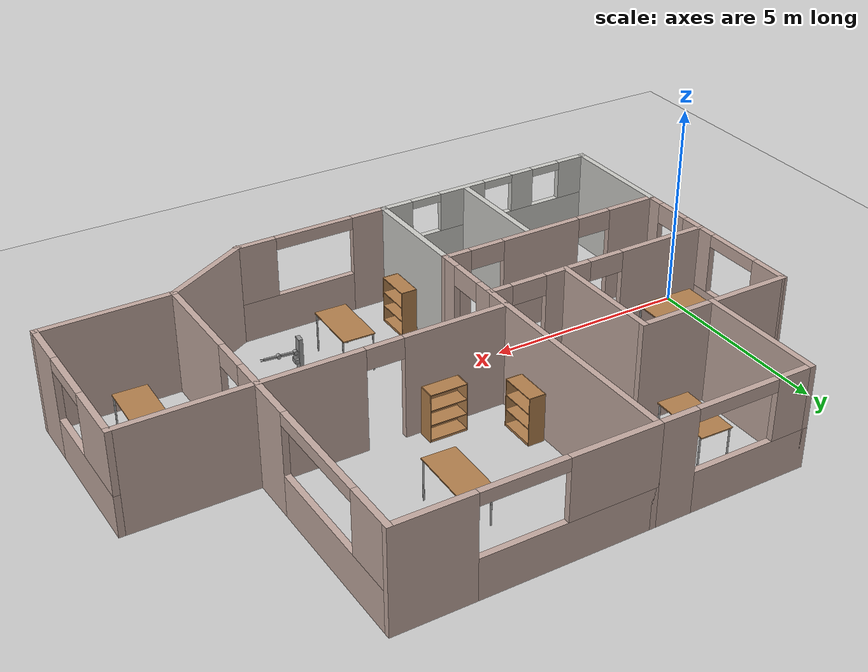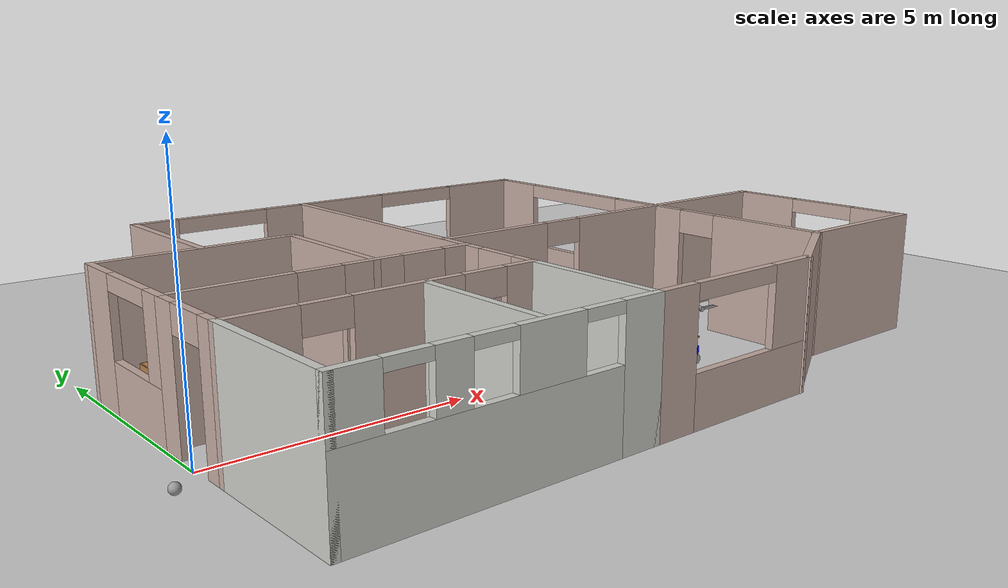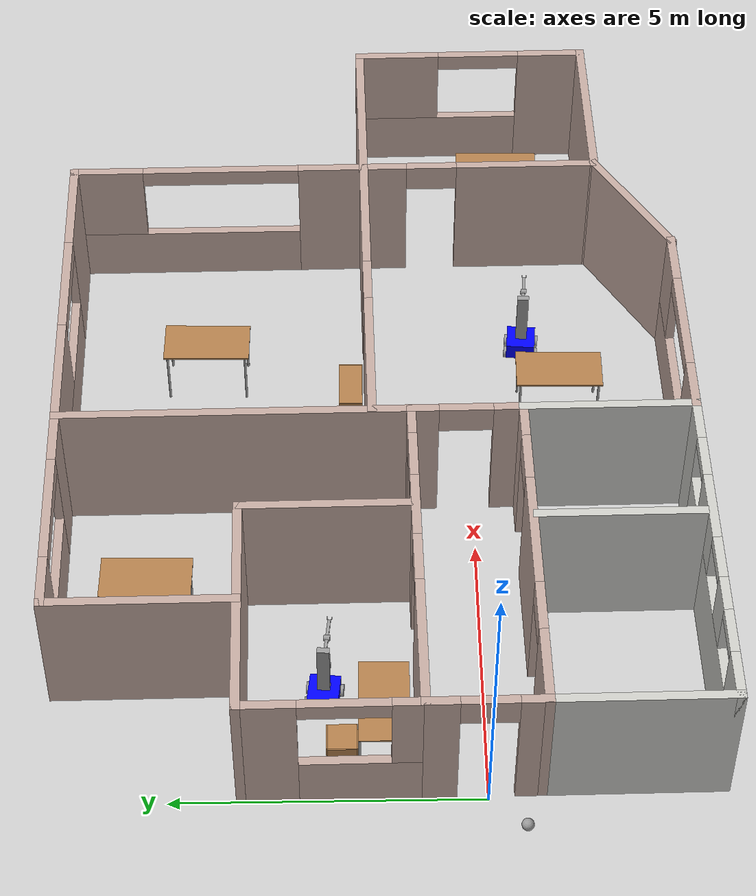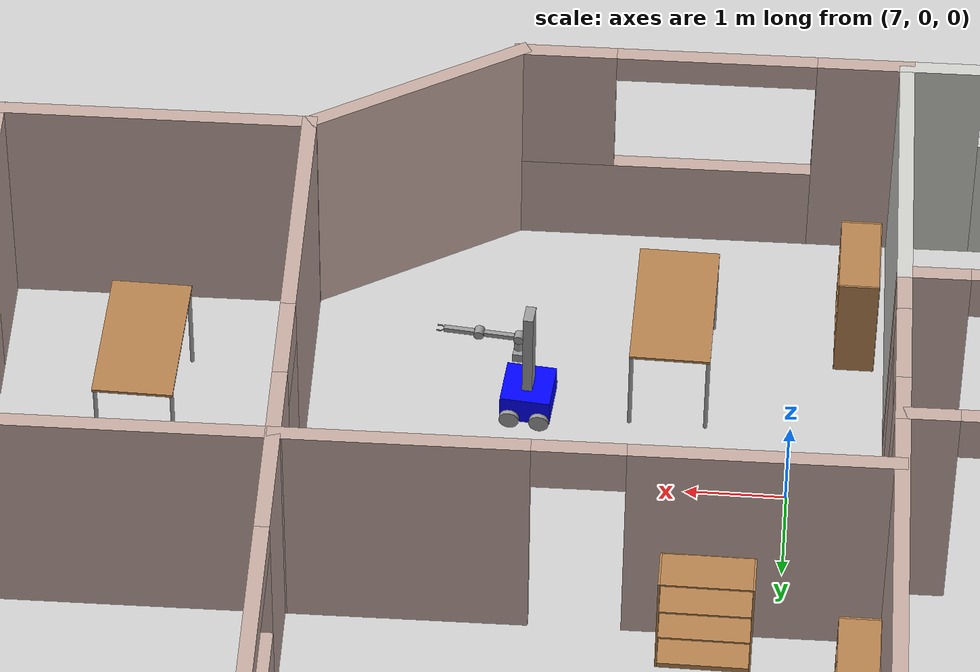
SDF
<sdf version="1.6">
 <world name="default">
  <plugin name="hello" filename="libhello.so"/>
  <light name="sun" type="directional">
   <pose>0 0 10 0 -0 0</pose>
   <diffuse>0.8 0.8 0.8 1</diffuse>
   <specular>0.2 0.2 0.2 1</specular>
   <attenuation>
    <range>1000</range>
    <constant>0.9</constant>
    <linear>0.01</linear>
    <quadratic>0.001</quadratic>
   </attenuation>
   <direction>-0.5 0.1 -0.9</direction>
  </light>
  <model name="ground_plane">
   <static>1</static>
   <link name="link">
    <collision name="collision">
     <geometry><plane><normal>0 0 1</normal><size>100 100</size></plane></geometry>
     <surface>
      <contact><collide_bitmask>65535</collide_bitmask></contact>
      <friction><ode><mu>100</mu><mu2>50</mu2></ode></friction>
     </surface>
    </collision>
    <visual name="visual">
     <cast_shadows>0</cast_shadows>
     <geometry><plane><normal>0 0 1</normal><size>100 100</size></plane></geometry>
     <material>
      <script><uri>file://media/materials/scripts/gazebo.material</uri><name>Gazebo/Grey</name></script>
     </material>
    </visual>
   </link>
  </model>
  <gravity>0 0 -9.8</gravity>
  <magnetic_field>6e-06 2.3e-05 -4.2e-05</magnetic_field>
  <atmosphere type="adiabatic"/>
  <physics name="default_physics" default="0" type="ode">
   <max_step_size>0.001</max_step_size>
   <real_time_factor>1</real_time_factor>
   <real_time_update_rate>1000</real_time_update_rate>
  </physics>
  <scene><ambient>0.4 0.4 0.4 1</ambient><background>0.7 0.7 0.7 1</background><shadows>1</shadows></scene>
  <audio><device>default</device></audio>
  <spherical_coordinates>
   <surface_model>EARTH_WGS84</surface_model>
   <latitude_deg>0</latitude_deg>
   <longitude_deg>0</longitude_deg>
   <elevation>0</elevation>
   <heading_deg>0</heading_deg>
  </spherical_coordinates>
  <model name="mybuilding">
   <pose>7.53126 1.66556 0 0 0 -3.13006</pose>
   <link name="Wall_0">
    <pose>1.56663 1.48627 0 0 -0 -1.5708</pose>
    <visual name="Wall_0_Visual_0">
     <pose>-0.7175 0 1.25 0 -0 0</pose>
     <geometry><box><size>0.565 0.15 2.5</size></box></geometry>
     <material>
      <script><uri>file://media/materials/scripts/gazebo.material</uri><name>Gazebo/Grey</name></script>
      <ambient>0.760784 0.662745 0.627451 1</ambient>
     </material>
     <meta><layer>0</layer></meta>
    </visual>
    <collision name="Wall_0_Collision_0">
     <geometry><box><size>0.565 0.15 2.5</size></box></geometry>
     <pose>-0.7175 0 1.25 0 -0 0</pose>
    </collision>
    <visual name="Wall_0_Visual_1">
     <pose>0.7325 0 1.25 0 -0 0</pose>
     <geometry><box><size>0.535 0.15 2.5</size></box></geometry>
     <material>
      <script><uri>file://media/materials/scripts/gazebo.material</uri><name>Gazebo/Grey</name></script>
      <ambient>0.760784 0.662745 0.627451 1</ambient>
     </material>
     <meta><layer>0</layer></meta>
    </visual>
    <collision name="Wall_0_Collision_1">
     <geometry><box><size>0.535 0.15 2.5</size></box></geometry>
     <pose>0.7325 0 1.25 0 -0 0</pose>
    </collision>
    <visual name="Wall_0_Visual_2">
     <pose>0.015 0 2.25 0 -0 0</pose>
     <geometry><box><size>0.9 0.15 0.5</size></box></geometry>
     <material>
      <script><uri>file://media/materials/scripts/gazebo.material</uri><name>Gazebo/Grey</name></script>
      <ambient>0.760784 0.662745 0.627451 1</ambient>
     </material>
     <meta><layer>0</layer></meta>
    </visual>
    <collision name="Wall_0_Collision_2">
     <geometry><box><size>0.9 0.15 0.5</size></box></geometry>
     <pose>0.015 0 2.25 0 -0 0</pose>
    </collision>
   </link>
   <link name="Wall_1">
    <pose>4.49163 0.561274 0 0 -0 0</pose>
    <visual name="Wall_1_Visual_0">
     <pose>-2.6925 0 1.25 0 -0 0</pose>
     <geometry><box><size>0.615 0.15 2.5</size></box></geometry>
     <material>
      <script><uri>file://media/materials/scripts/gazebo.material</uri><name>Gazebo/Grey</name></script>
      <ambient>0.760784 0.662745 0.627451 1</ambient>
     </material>
     <meta><layer>0</layer></meta>
    </visual>
    <collision name="Wall_1_Collision_0">
     <geometry><box><size>0.615 0.15 2.5</size></box></geometry>
     <pose>-2.6925 0 1.25 0 -0 0</pose>
    </collision>
    <visual name="Wall_1_Visual_1">
     <pose>-0.88 0 1.25 0 -0 0</pose>
     <geometry><box><size>1.21 0.15 2.5</size></box></geometry>
     <material>
      <script><uri>file://media/materials/scripts/gazebo.material</uri><name>Gazebo/Grey</name></script>
      <ambient>0.760784 0.662745 0.627451 1</ambient>
     </material>
     <meta><layer>0</layer></meta>
    </visual>
    <collision name="Wall_1_Collision_1">
     <geometry><box><size>1.21 0.15 2.5</size></box></geometry>
     <pose>-0.88 0 1.25 0 -0 0</pose>
    </collision>
    <visual name="Wall_1_Visual_2">
     <pose>1.8125 0 1.25 0 -0 0</pose>
     <geometry><box><size>2.375 0.15 2.5</size></box></geometry>
     <material>
      <script><uri>file://media/materials/scripts/gazebo.material</uri><name>Gazebo/Grey</name></script>
      <ambient>0.760784 0.662745 0.627451 1</ambient>
     </material>
     <meta><layer>0</layer></meta>
    </visual>
    <collision name="Wall_1_Collision_2">
     <geometry><box><size>2.375 0.15 2.5</size></box></geometry>
     <pose>1.8125 0 1.25 0 -0 0</pose>
    </collision>
    <visual name="Wall_1_Visual_3">
     <pose>-1.935 0 2.25 0 -0 0</pose>
     <geometry><box><size>0.9 0.15 0.5</size></box></geometry>
     <material>
      <script><uri>file://media/materials/scripts/gazebo.material</uri><name>Gazebo/Grey</name></script>
      <ambient>0.760784 0.662745 0.627451 1</ambient>
     </material>
     <meta><layer>0</layer></meta>
    </visual>
    <collision name="Wall_1_Collision_3">
     <geometry><box><size>0.9 0.15 0.5</size></box></geometry>
     <pose>-1.935 0 2.25 0 -0 0</pose>
    </collision>
    <visual name="Wall_1_Visual_4">
     <pose>0.175 0 2.25 0 -0 0</pose>
     <geometry><box><size>0.9 0.15 0.5</size></box></geometry>
     <material>
      <script><uri>file://media/materials/scripts/gazebo.material</uri><name>Gazebo/Grey</name></script>
      <ambient>0.760784 0.662745 0.627451 1</ambient>
     </material>
     <meta><layer>0</layer></meta>
    </visual>
    <collision name="Wall_1_Collision_4">
     <geometry><box><size>0.9 0.15 0.5</size></box></geometry>
     <pose>0.175 0 2.25 0 -0 0</pose>
    </collision>
   </link>
   <link name="Wall_10">
    <pose>3.49163 -5.28873 0 0 -0 0</pose>
    <visual name="Wall_10_Visual_0">
     <pose>-1.48371 0 1.25 0 -0 0</pose>
     <geometry><box><size>1.03258 0.15 2.5</size></box></geometry>
     <material>
      <script><uri>file://media/materials/scripts/gazebo.material</uri><name>Gazebo/Grey</name></script>
      <ambient>0.760784 0.662745 0.627451 1</ambient>
     </material>
     <meta><layer>0</layer></meta>
    </visual>
    <collision name="Wall_10_Collision_0">
     <geometry><box><size>1.03258 0.15 2.5</size></box></geometry>
     <pose>-1.48371 0 1.25 0 -0 0</pose>
    </collision>
    <visual name="Wall_10_Visual_1">
     <pose>0.516287 0 0.5 0 -0 0</pose>
     <geometry><box><size>2.96742 0.15 1</size></box></geometry>
     <material>
      <script><uri>file://media/materials/scripts/gazebo.material</uri><name>Gazebo/Grey</name></script>
      <ambient>0.760784 0.662745 0.627451 1</ambient>
     </material>
     <meta><layer>0</layer></meta>
    </visual>
    <collision name="Wall_10_Collision_1">
     <geometry><box><size>2.96742 0.15 1</size></box></geometry>
     <pose>0.516287 0 0.5 0 -0 0</pose>
    </collision>
    <visual name="Wall_10_Visual_2">
     <pose>1.51629 0 1.75 0 -0 0</pose>
     <geometry><box><size>0.967425 0.15 1.5</size></box></geometry>
     <material>
      <script><uri>file://media/materials/scripts/gazebo.material</uri><name>Gazebo/Grey</name></script>
      <ambient>0.760784 0.662745 0.627451 1</ambient>
     </material>
     <meta><layer>0</layer></meta>
    </visual>
    <collision name="Wall_10_Collision_2">
     <geometry><box><size>0.967425 0.15 1.5</size></box></geometry>
     <pose>1.51629 0 1.75 0 -0 0</pose>
    </collision>
    <visual name="Wall_10_Visual_3">
     <pose>0.032575 0 2.35 0 -0 0</pose>
     <geometry><box><size>2 0.15 0.3</size></box></geometry>
     <material>
      <script><uri>file://media/materials/scripts/gazebo.material</uri><name>Gazebo/Grey</name></script>
      <ambient>0.760784 0.662745 0.627451 1</ambient>
     </material>
     <meta><layer>0</layer></meta>
    </visual>
    <collision name="Wall_10_Collision_3">
     <geometry><box><size>2 0.15 0.3</size></box></geometry>
     <pose>0.032575 0 2.35 0 -0 0</pose>
    </collision>
   </link>
   <link name="Wall_11">
    <collision name="Wall_11_Collision">
     <geometry><box><size>3.165 0.15 2.5</size></box></geometry>
     <pose>0 0 1.25 0 -0 0</pose>
    </collision>
    <visual name="Wall_11_Visual">
     <pose>0 0 1.25 0 -0 0</pose>
     <geometry><box><size>3.165 0.15 2.5</size></box></geometry>
     <material>
      <script><uri>file://media/materials/scripts/gazebo.material</uri><name>Gazebo/Grey</name></script>
      <ambient>0.760784 0.662745 0.627451 1</ambient>
     </material>
     <meta><layer>0</layer></meta>
    </visual>
    <pose>5.41663 -3.78123 0 0 -0 1.5708</pose>
   </link>
   <link name="Wall_13">
    <collision name="Wall_13_Collision">
     <geometry><box><size>3 0.15 2.5</size></box></geometry>
     <pose>0 0 1.25 0 -0 0</pose>
    </collision>
    <visual name="Wall_13_Visual">
     <pose>0 0 1.25 0 -0 0</pose>
     <geometry><box><size>3 0.15 2.5</size></box></geometry>
     <material>
      <script><uri>file://media/materials/scripts/gazebo.material</uri><name>Gazebo/CeilingTiled</name></script>
      <ambient>0.760784 0.662745 0.627451 1</ambient>
     </material>
     <meta><layer>0</layer></meta>
    </visual>
    <pose>1.56663 3.83627 0 0 -0 1.5708</pose>
   </link>
   <link name="Wall_14">
    <pose>4.49163 5.26127 0 0 -0 0</pose>
    <visual name="Wall_14_Visual_0">
     <pose>-2.57832 0 1.25 0 -0 0</pose>
     <geometry><box><size>0.843365 0.15 2.5</size></box></geometry>
     <material>
      <script><uri>file://media/materials/scripts/gazebo.material</uri><name>Gazebo/CeilingTiled</name></script>
      <ambient>1 1 1 1</ambient>
     </material>
     <meta><layer>0</layer></meta>
    </visual>
    <collision name="Wall_14_Collision_0">
     <geometry><box><size>0.843365 0.15 2.5</size></box></geometry>
     <pose>-2.57832 0 1.25 0 -0 0</pose>
    </collision>
    <visual name="Wall_14_Visual_1">
     <pose>0.421683 0 0.75 0 -0 0</pose>
     <geometry><box><size>5.15663 0.15 1.5</size></box></geometry>
     <material>
      <script><uri>file://media/materials/scripts/gazebo.material</uri><name>Gazebo/CeilingTiled</name></script>
      <ambient>1 1 1 1</ambient>
     </material>
     <meta><layer>0</layer></meta>
    </visual>
    <collision name="Wall_14_Collision_1">
     <geometry><box><size>5.15663 0.15 1.5</size></box></geometry>
     <pose>0.421683 0 0.75 0 -0 0</pose>
    </collision>
    <visual name="Wall_14_Visual_2">
     <pose>-0.718472 0 2 0 -0 0</pose>
     <geometry><box><size>1.27632 0.15 1</size></box></geometry>
     <material>
      <script><uri>file://media/materials/scripts/gazebo.material</uri><name>Gazebo/CeilingTiled</name></script>
      <ambient>1 1 1 1</ambient>
     </material>
     <meta><layer>0</layer></meta>
    </visual>
    <collision name="Wall_14_Collision_2">
     <geometry><box><size>1.27632 0.15 1</size></box></geometry>
     <pose>-0.718472 0 2 0 -0 0</pose>
    </collision>
    <visual name="Wall_14_Visual_3">
     <pose>1.03384 0 2 0 -0 0</pose>
     <geometry><box><size>0.6283 0.15 1</size></box></geometry>
     <material>
      <script><uri>file://media/materials/scripts/gazebo.material</uri><name>Gazebo/CeilingTiled</name></script>
      <ambient>1 1 1 1</ambient>
     </material>
     <meta><layer>0</layer></meta>
    </visual>
    <collision name="Wall_14_Collision_3">
     <geometry><box><size>0.6283 0.15 1</size></box></geometry>
     <pose>1.03384 0 2 0 -0 0</pose>
    </collision>
    <visual name="Wall_14_Visual_4">
     <pose>2.574 0 2 0 -0 0</pose>
     <geometry><box><size>0.85201 0.15 1</size></box></geometry>
     <material>
      <script><uri>file://media/materials/scripts/gazebo.material</uri><name>Gazebo/CeilingTiled</name></script>
      <ambient>1 1 1 1</ambient>
     </material>
     <meta><layer>0</layer></meta>
    </visual>
    <collision name="Wall_14_Collision_4">
     <geometry><box><size>0.85201 0.15 1</size></box></geometry>
     <pose>2.574 0 2 0 -0 0</pose>
    </collision>
    <visual name="Wall_14_Visual_5">
     <pose>-1.75663 0 2.4 0 -0 0</pose>
     <geometry><box><size>0.8 0.15 0.2</size></box></geometry>
     <material>
      <script><uri>file://media/materials/scripts/gazebo.material</uri><name>Gazebo/CeilingTiled</name></script>
      <ambient>1 1 1 1</ambient>
     </material>
     <meta><layer>0</layer></meta>
    </visual>
    <collision name="Wall_14_Collision_5">
     <geometry><box><size>0.8 0.15 0.2</size></box></geometry>
     <pose>-1.75663 0 2.4 0 -0 0</pose>
    </collision>
    <visual name="Wall_14_Visual_6">
     <pose>0.31969 0 2.4 0 -0 0</pose>
     <geometry><box><size>0.8 0.15 0.2</size></box></geometry>
     <material>
      <script><uri>file://media/materials/scripts/gazebo.material</uri><name>Gazebo/CeilingTiled</name></script>
      <ambient>1 1 1 1</ambient>
     </material>
     <meta><layer>0</layer></meta>
    </visual>
    <collision name="Wall_14_Collision_6">
     <geometry><box><size>0.8 0.15 0.2</size></box></geometry>
     <pose>0.31969 0 2.4 0 -0 0</pose>
    </collision>
    <visual name="Wall_14_Visual_7">
     <pose>1.74799 0 2.4 0 -0 0</pose>
     <geometry><box><size>0.8 0.15 0.2</size></box></geometry>
     <material>
      <script><uri>file://media/materials/scripts/gazebo.material</uri><name>Gazebo/CeilingTiled</name></script>
      <ambient>1 1 1 1</ambient>
     </material>
     <meta><layer>0</layer></meta>
    </visual>
    <collision name="Wall_14_Collision_7">
     <geometry><box><size>0.8 0.15 0.2</size></box></geometry>
     <pose>1.74799 0 2.4 0 -0 0</pose>
    </collision>
   </link>
   <link name="Wall_15">
    <collision name="Wall_15_Collision">
     <geometry><box><size>3 0.15 2.5</size></box></geometry>
     <pose>0 0 1.25 0 -0 0</pose>
    </collision>
    <visual name="Wall_15_Visual">
     <pose>0 0 1.25 0 -0 0</pose>
     <geometry><box><size>3 0.15 2.5</size></box></geometry>
     <material>
      <script><uri>file://media/materials/scripts/gazebo.material</uri><name>Gazebo/CeilingTiled</name></script>
      <ambient>1 1 1 1</ambient>
     </material>
     <meta><layer>0</layer></meta>
    </visual>
    <pose>7.41663 3.83627 0 0 -0 -1.5708</pose>
   </link>
   <link name="Wall_17">
    <collision name="Wall_17_Collision">
     <geometry><box><size>2.81 0.15 2.5</size></box></geometry>
     <pose>0 0 1.25 0 -0 0</pose>
    </collision>
    <visual name="Wall_17_Visual">
     <pose>0 0 1.25 0 -0 0</pose>
     <geometry><box><size>2.81 0.15 2.5</size></box></geometry>
     <material>
      <script><uri>file://media/materials/scripts/gazebo.material</uri><name>Gazebo/CeilingTiled</name></script>
      <ambient>1 1 1 1</ambient>
     </material>
     <meta><layer>0</layer></meta>
    </visual>
    <pose>3.85863 3.79127 0 0 -0 1.5708</pose>
   </link>
   <link name="Wall_19">
    <pose>-0.358374 5.26127 0 0 -0 3.14159</pose>
    <visual name="Wall_19_Visual_0">
     <pose>-1.51488 0 1.25 0 -0 0</pose>
     <geometry><box><size>0.970244 0.15 2.5</size></box></geometry>
     <material>
      <script><uri>file://media/materials/scripts/gazebo.material</uri><name>Gazebo/Grey</name></script>
      <ambient>0.760784 0.662745 0.627451 1</ambient>
     </material>
     <meta><layer>0</layer></meta>
    </visual>
    <collision name="Wall_19_Collision_0">
     <geometry><box><size>0.970244 0.15 2.5</size></box></geometry>
     <pose>-1.51488 0 1.25 0 -0 0</pose>
    </collision>
    <visual name="Wall_19_Visual_1">
     <pose>0.485122 0 0.5 0 -0 0</pose>
     <geometry><box><size>3.02976 0.15 1</size></box></geometry>
     <material>
      <script><uri>file://media/materials/scripts/gazebo.material</uri><name>Gazebo/Grey</name></script>
      <ambient>0.760784 0.662745 0.627451 1</ambient>
     </material>
     <meta><layer>0</layer></meta>
    </visual>
    <collision name="Wall_19_Collision_1">
     <geometry><box><size>3.02976 0.15 1</size></box></geometry>
     <pose>0.485122 0 0.5 0 -0 0</pose>
    </collision>
    <visual name="Wall_19_Visual_2">
     <pose>1.48512 0 1.75 0 -0 0</pose>
     <geometry><box><size>1.02976 0.15 1.5</size></box></geometry>
     <material>
      <script><uri>file://media/materials/scripts/gazebo.material</uri><name>Gazebo/Grey</name></script>
      <ambient>0.760784 0.662745 0.627451 1</ambient>
     </material>
     <meta><layer>0</layer></meta>
    </visual>
    <collision name="Wall_19_Collision_2">
     <geometry><box><size>1.02976 0.15 1.5</size></box></geometry>
     <pose>1.48512 0 1.75 0 -0 0</pose>
    </collision>
    <visual name="Wall_19_Visual_3">
     <pose>-0.029756 0 2.35 0 -0 0</pose>
     <geometry><box><size>2 0.15 0.3</size></box></geometry>
     <material>
      <script><uri>file://media/materials/scripts/gazebo.material</uri><name>Gazebo/Grey</name></script>
      <ambient>0.760784 0.662745 0.627451 1</ambient>
     </material>
     <meta><layer>0</layer></meta>
    </visual>
    <collision name="Wall_19_Collision_3">
     <geometry><box><size>2 0.15 0.3</size></box></geometry>
     <pose>-0.029756 0 2.35 0 -0 0</pose>
    </collision>
   </link>
   <link name="Wall_2">
    <pose>7.41663 1.48627 0 0 -0 1.5708</pose>
    <visual name="Wall_2_Visual_0">
     <pose>-0.7025 0 1.25 0 -0 0</pose>
     <geometry><box><size>0.595 0.15 2.5</size></box></geometry>
     <material>
      <script><uri>file://media/materials/scripts/gazebo.material</uri><name>Gazebo/Grey</name></script>
      <ambient>0.760784 0.662745 0.627451 1</ambient>
     </material>
     <meta><layer>0</layer></meta>
    </visual>
    <collision name="Wall_2_Collision_0">
     <geometry><box><size>0.595 0.15 2.5</size></box></geometry>
     <pose>-0.7025 0 1.25 0 -0 0</pose>
    </collision>
    <visual name="Wall_2_Visual_1">
     <pose>0.7475 0 1.25 0 -0 0</pose>
     <geometry><box><size>0.505 0.15 2.5</size></box></geometry>
     <material>
      <script><uri>file://media/materials/scripts/gazebo.material</uri><name>Gazebo/Grey</name></script>
      <ambient>0.760784 0.662745 0.627451 1</ambient>
     </material>
     <meta><layer>0</layer></meta>
    </visual>
    <collision name="Wall_2_Collision_1">
     <geometry><box><size>0.505 0.15 2.5</size></box></geometry>
     <pose>0.7475 0 1.25 0 -0 0</pose>
    </collision>
    <visual name="Wall_2_Visual_2">
     <pose>0.045 0 2.25 0 -0 0</pose>
     <geometry><box><size>0.9 0.15 0.5</size></box></geometry>
     <material>
      <script><uri>file://media/materials/scripts/gazebo.material</uri><name>Gazebo/Grey</name></script>
      <ambient>0.760784 0.662745 0.627451 1</ambient>
     </material>
     <meta><layer>0</layer></meta>
    </visual>
    <collision name="Wall_2_Collision_2">
     <geometry><box><size>0.9 0.15 0.5</size></box></geometry>
     <pose>0.045 0 2.25 0 -0 0</pose>
    </collision>
   </link>
   <link name="Wall_20">
    <collision name="Wall_20_Collision">
     <geometry><box><size>2.5 0.15 2.5</size></box></geometry>
     <pose>0 0 1.25 0 -0 0</pose>
    </collision>
    <visual name="Wall_20_Visual">
     <pose>0 0 1.25 0 -0 0</pose>
     <geometry><box><size>2.5 0.15 2.5</size></box></geometry>
     <material>
      <script><uri>file://media/materials/scripts/gazebo.material</uri><name>Gazebo/Grey</name></script>
      <ambient>0.760784 0.662745 0.627451 1</ambient>
     </material>
     <meta><layer>0</layer></meta>
    </visual>
    <pose>-3.30096 4.67377 0 0 -0 -2.61799</pose>
   </link>
   <link name="Wall_21">
    <pose>-4.31846 -0.601226 0 0 -0 -1.57078</pose>
    <visual name="Wall_21_Visual_0">
     <pose>-3.47885 0 1.25 0 -0 0</pose>
     <geometry><box><size>2.5673 0.15 2.5</size></box></geometry>
     <material>
      <script><uri>file://media/materials/scripts/gazebo.material</uri><name>Gazebo/Grey</name></script>
      <ambient>0.760784 0.662745 0.627451 1</ambient>
     </material>
     <meta><layer>0</layer></meta>
    </visual>
    <collision name="Wall_21_Collision_0">
     <geometry><box><size>2.5673 0.15 2.5</size></box></geometry>
     <pose>-3.47885 0 1.25 0 -0 0</pose>
    </collision>
    <visual name="Wall_21_Visual_1">
     <pose>-0.317714 0 1.25 0 -0 0</pose>
     <geometry><box><size>1.95498 0.15 2.5</size></box></geometry>
     <material>
      <script><uri>file://media/materials/scripts/gazebo.material</uri><name>Gazebo/Grey</name></script>
      <ambient>0.760784 0.662745 0.627451 1</ambient>
     </material>
     <meta><layer>0</layer></meta>
    </visual>
    <collision name="Wall_21_Collision_1">
     <geometry><box><size>1.95498 0.15 2.5</size></box></geometry>
     <pose>-0.317714 0 1.25 0 -0 0</pose>
    </collision>
    <visual name="Wall_21_Visual_2">
     <pose>2.71114 0 0.5 0 -0 0</pose>
     <geometry><box><size>4.10272 0.15 1</size></box></geometry>
     <material>
      <script><uri>file://media/materials/scripts/gazebo.material</uri><name>Gazebo/Grey</name></script>
      <ambient>0.760784 0.662745 0.627451 1</ambient>
     </material>
     <meta><layer>0</layer></meta>
    </visual>
    <collision name="Wall_21_Collision_2">
     <geometry><box><size>4.10272 0.15 1</size></box></geometry>
     <pose>2.71114 0 0.5 0 -0 0</pose>
    </collision>
    <visual name="Wall_21_Visual_3">
     <pose>4.11114 0 1.75 0 -0 0</pose>
     <geometry><box><size>1.30272 0.15 1.5</size></box></geometry>
     <material>
      <script><uri>file://media/materials/scripts/gazebo.material</uri><name>Gazebo/Grey</name></script>
      <ambient>0.760784 0.662745 0.627451 1</ambient>
     </material>
     <meta><layer>0</layer></meta>
    </visual>
    <collision name="Wall_21_Collision_3">
     <geometry><box><size>1.30272 0.15 1.5</size></box></geometry>
     <pose>4.11114 0 1.75 0 -0 0</pose>
    </collision>
    <visual name="Wall_21_Visual_4">
     <pose>-1.7452 0 2.25 0 -0 0</pose>
     <geometry><box><size>0.9 0.15 0.5</size></box></geometry>
     <material>
      <script><uri>file://media/materials/scripts/gazebo.material</uri><name>Gazebo/Grey</name></script>
      <ambient>0.760784 0.662745 0.627451 1</ambient>
     </material>
     <meta><layer>0</layer></meta>
    </visual>
    <collision name="Wall_21_Collision_4">
     <geometry><box><size>0.9 0.15 0.5</size></box></geometry>
     <pose>-1.7452 0 2.25 0 -0 0</pose>
    </collision>
    <visual name="Wall_21_Visual_5">
     <pose>2.05978 0 2.35 0 -0 0</pose>
     <geometry><box><size>2.8 0.15 0.3</size></box></geometry>
     <material>
      <script><uri>file://media/materials/scripts/gazebo.material</uri><name>Gazebo/Grey</name></script>
      <ambient>0.760784 0.662745 0.627451 1</ambient>
     </material>
     <meta><layer>0</layer></meta>
    </visual>
    <collision name="Wall_21_Collision_5">
     <geometry><box><size>2.8 0.15 0.3</size></box></geometry>
     <pose>2.05978 0 2.35 0 -0 0</pose>
    </collision>
   </link>
   <link name="Wall_22">
    <pose>-1.37587 -5.28873 0 0 -0 0</pose>
    <visual name="Wall_22_Visual_0">
     <pose>-2.06844 0 1.25 0 -0 0</pose>
     <geometry><box><size>1.89834 0.15 2.5</size></box></geometry>
     <material>
      <script><uri>file://media/materials/scripts/gazebo.material</uri><name>Gazebo/Grey</name></script>
      <ambient>0.760784 0.662745 0.627451 1</ambient>
     </material>
     <meta><layer>0</layer></meta>
    </visual>
    <collision name="Wall_22_Collision_0">
     <geometry><box><size>1.89834 0.15 2.5</size></box></geometry>
     <pose>-2.06844 0 1.25 0 -0 0</pose>
    </collision>
    <visual name="Wall_22_Visual_1">
     <pose>0.949169 0 0.5 0 -0 0</pose>
     <geometry><box><size>4.13687 0.15 1</size></box></geometry>
     <material>
      <script><uri>file://media/materials/scripts/gazebo.material</uri><name>Gazebo/Grey</name></script>
      <ambient>0.760784 0.662745 0.627451 1</ambient>
     </material>
     <meta><layer>0</layer></meta>
    </visual>
    <collision name="Wall_22_Collision_1">
     <geometry><box><size>4.13687 0.15 1</size></box></geometry>
     <pose>0.949169 0 0.5 0 -0 0</pose>
    </collision>
    <visual name="Wall_22_Visual_2">
     <pose>1.94917 0 1.75 0 -0 0</pose>
     <geometry><box><size>2.13687 0.15 1.5</size></box></geometry>
     <material>
      <script><uri>file://media/materials/scripts/gazebo.material</uri><name>Gazebo/Grey</name></script>
      <ambient>0.760784 0.662745 0.627451 1</ambient>
     </material>
     <meta><layer>0</layer></meta>
    </visual>
    <collision name="Wall_22_Collision_2">
     <geometry><box><size>2.13687 0.15 1.5</size></box></geometry>
     <pose>1.94917 0 1.75 0 -0 0</pose>
    </collision>
    <visual name="Wall_22_Visual_3">
     <pose>-0.119267 0 2.35 0 -0 0</pose>
     <geometry><box><size>2 0.15 0.3</size></box></geometry>
     <material>
      <script><uri>file://media/materials/scripts/gazebo.material</uri><name>Gazebo/Grey</name></script>
      <ambient>0.760784 0.662745 0.627451 1</ambient>
     </material>
     <meta><layer>0</layer></meta>
    </visual>
    <collision name="Wall_22_Collision_3">
     <geometry><box><size>2 0.15 0.3</size></box></geometry>
     <pose>-0.119267 0 2.35 0 -0 0</pose>
    </collision>
   </link>
   <link name="Wall_24">
    <pose>-1.37819 -0.082545 0 0 -0 6.2e-05</pose>
    <visual name="Wall_24_Visual_0">
     <pose>-1.76034 0 1.25 0 -0 0</pose>
     <geometry><box><size>2.47931 0.15 2.5</size></box></geometry>
     <material>
      <script><uri>file://media/materials/scripts/gazebo.material</uri><name>Gazebo/Grey</name></script>
      <ambient>0.760784 0.662745 0.627451 1</ambient>
     </material>
     <meta><layer>0</layer></meta>
    </visual>
    <collision name="Wall_24_Collision_0">
     <geometry><box><size>2.47931 0.15 2.5</size></box></geometry>
     <pose>-1.76034 0 1.25 0 -0 0</pose>
    </collision>
    <visual name="Wall_24_Visual_1">
     <pose>1.68966 0 1.25 0 -0 0</pose>
     <geometry><box><size>2.62069 0.15 2.5</size></box></geometry>
     <material>
      <script><uri>file://media/materials/scripts/gazebo.material</uri><name>Gazebo/Grey</name></script>
      <ambient>0.760784 0.662745 0.627451 1</ambient>
     </material>
     <meta><layer>0</layer></meta>
    </visual>
    <collision name="Wall_24_Collision_1">
     <geometry><box><size>2.62069 0.15 2.5</size></box></geometry>
     <pose>1.68966 0 1.25 0 -0 0</pose>
    </collision>
    <visual name="Wall_24_Visual_2">
     <pose>-0.070687 0 2.25 0 -0 0</pose>
     <geometry><box><size>0.9 0.15 0.5</size></box></geometry>
     <material>
      <script><uri>file://media/materials/scripts/gazebo.material</uri><name>Gazebo/Grey</name></script>
      <ambient>0.760784 0.662745 0.627451 1</ambient>
     </material>
     <meta><layer>0</layer></meta>
    </visual>
    <collision name="Wall_24_Collision_2">
     <geometry><box><size>0.9 0.15 0.5</size></box></geometry>
     <pose>-0.070687 0 2.25 0 -0 0</pose>
    </collision>
   </link>
   <link name="Wall_26">
    <collision name="Wall_26_Collision">
     <geometry><box><size>3.25 0.15 2.5</size></box></geometry>
     <pose>0 0 1.25 0 -0 0</pose>
    </collision>
    <visual name="Wall_26_Visual">
     <pose>0 0 1.25 0 -0 0</pose>
     <geometry><box><size>3.25 0.15 2.5</size></box></geometry>
     <material>
      <script><uri>file://media/materials/scripts/gazebo.material</uri><name>Gazebo/Grey</name></script>
      <ambient>0.760784 0.662745 0.627451 1</ambient>
     </material>
     <meta><layer>0</layer></meta>
    </visual>
    <pose>-5.86853 4.08627 0 0 -0 3.14159</pose>
   </link>
   <link name="Wall_27">
    <pose>-7.41845 2.00177 0 0 -0 -1.57076</pose>
    <visual name="Wall_27_Visual_0">
     <pose>-1.53124 0 1.25 0 -0 0</pose>
     <geometry><box><size>1.25652 0.15 2.5</size></box></geometry>
     <material>
      <script><uri>file://media/materials/scripts/gazebo.material</uri><name>Gazebo/Grey</name></script>
      <ambient>0.760784 0.662745 0.627451 1</ambient>
     </material>
     <meta><layer>0</layer></meta>
    </visual>
    <collision name="Wall_27_Collision_0">
     <geometry><box><size>1.25652 0.15 2.5</size></box></geometry>
     <pose>-1.53124 0 1.25 0 -0 0</pose>
    </collision>
    <visual name="Wall_27_Visual_1">
     <pose>0.628263 0 0.5 0 -0 0</pose>
     <geometry><box><size>3.06248 0.15 1</size></box></geometry>
     <material>
      <script><uri>file://media/materials/scripts/gazebo.material</uri><name>Gazebo/Grey</name></script>
      <ambient>0.760784 0.662745 0.627451 1</ambient>
     </material>
     <meta><layer>0</layer></meta>
    </visual>
    <collision name="Wall_27_Collision_1">
     <geometry><box><size>3.06248 0.15 1</size></box></geometry>
     <pose>0.628263 0 0.5 0 -0 0</pose>
    </collision>
    <visual name="Wall_27_Visual_2">
     <pose>1.37826 0 1.75 0 -0 0</pose>
     <geometry><box><size>1.56248 0.15 1.5</size></box></geometry>
     <material>
      <script><uri>file://media/materials/scripts/gazebo.material</uri><name>Gazebo/Grey</name></script>
      <ambient>0.760784 0.662745 0.627451 1</ambient>
     </material>
     <meta><layer>0</layer></meta>
    </visual>
    <collision name="Wall_27_Collision_2">
     <geometry><box><size>1.56248 0.15 1.5</size></box></geometry>
     <pose>1.37826 0 1.75 0 -0 0</pose>
    </collision>
    <visual name="Wall_27_Visual_3">
     <pose>-0.152975 0 2.35 0 -0 0</pose>
     <geometry><box><size>1.5 0.15 0.3</size></box></geometry>
     <material>
      <script><uri>file://media/materials/scripts/gazebo.material</uri><name>Gazebo/Grey</name></script>
      <ambient>0.760784 0.662745 0.627451 1</ambient>
     </material>
     <meta><layer>0</layer></meta>
    </visual>
    <collision name="Wall_27_Collision_3">
     <geometry><box><size>1.5 0.15 0.3</size></box></geometry>
     <pose>-0.152975 0 2.35 0 -0 0</pose>
    </collision>
   </link>
   <link name="Wall_28">
    <collision name="Wall_28_Collision">
     <geometry><box><size>3.265 0.15 2.5</size></box></geometry>
     <pose>0 0 1.25 0 -0 0</pose>
    </collision>
    <visual name="Wall_28_Visual">
     <pose>0 0 1.25 0 -0 0</pose>
     <geometry><box><size>3.265 0.15 2.5</size></box></geometry>
     <material>
      <script><uri>file://media/materials/scripts/gazebo.material</uri><name>Gazebo/Grey</name></script>
      <ambient>0.760784 0.662745 0.627451 1</ambient>
     </material>
     <meta><layer>0</layer></meta>
    </visual>
    <pose>-5.86087 -0.082726 0 0 -0 0</pose>
   </link>
   <link name="Wall_3">
    <pose>4.49163 2.41127 0 0 -0 3.14159</pose>
    <visual name="Wall_3_Visual_0">
     <pose>-2.3175 0 1.25 0 -0 0</pose>
     <geometry><box><size>1.365 0.15 2.5</size></box></geometry>
     <material>
      <script><uri>file://media/materials/scripts/gazebo.material</uri><name>Gazebo/Grey</name></script>
      <ambient>0.760784 0.662745 0.627451 1</ambient>
     </material>
     <meta><layer>0</layer></meta>
    </visual>
    <collision name="Wall_3_Collision_0">
     <geometry><box><size>1.365 0.15 2.5</size></box></geometry>
     <pose>-2.3175 0 1.25 0 -0 0</pose>
    </collision>
    <visual name="Wall_3_Visual_1">
     <pose>0.325 0 1.25 0 -0 0</pose>
     <geometry><box><size>2.12 0.15 2.5</size></box></geometry>
     <material>
      <script><uri>file://media/materials/scripts/gazebo.material</uri><name>Gazebo/Grey</name></script>
      <ambient>0.760784 0.662745 0.627451 1</ambient>
     </material>
     <meta><layer>0</layer></meta>
    </visual>
    <collision name="Wall_3_Collision_1">
     <geometry><box><size>2.12 0.15 2.5</size></box></geometry>
     <pose>0.325 0 1.25 0 -0 0</pose>
    </collision>
    <visual name="Wall_3_Visual_2">
     <pose>2.6425 0 1.25 0 -0 0</pose>
     <geometry><box><size>0.715 0.15 2.5</size></box></geometry>
     <material>
      <script><uri>file://media/materials/scripts/gazebo.material</uri><name>Gazebo/Grey</name></script>
      <ambient>0.760784 0.662745 0.627451 1</ambient>
     </material>
     <meta><layer>0</layer></meta>
    </visual>
    <collision name="Wall_3_Collision_2">
     <geometry><box><size>0.715 0.15 2.5</size></box></geometry>
     <pose>2.6425 0 1.25 0 -0 0</pose>
    </collision>
    <visual name="Wall_3_Visual_3">
     <pose>-1.185 0 2.25 0 -0 0</pose>
     <geometry><box><size>0.9 0.15 0.5</size></box></geometry>
     <material>
      <script><uri>file://media/materials/scripts/gazebo.material</uri><name>Gazebo/Grey</name></script>
      <ambient>0.760784 0.662745 0.627451 1</ambient>
     </material>
     <meta><layer>0</layer></meta>
    </visual>
    <collision name="Wall_3_Collision_3">
     <geometry><box><size>0.9 0.15 0.5</size></box></geometry>
     <pose>-1.185 0 2.25 0 -0 0</pose>
    </collision>
    <visual name="Wall_3_Visual_4">
     <pose>1.835 0 2.25 0 -0 0</pose>
     <geometry><box><size>0.9 0.15 0.5</size></box></geometry>
     <material>
      <script><uri>file://media/materials/scripts/gazebo.material</uri><name>Gazebo/Grey</name></script>
      <ambient>0.760784 0.662745 0.627451 1</ambient>
     </material>
     <meta><layer>0</layer></meta>
    </visual>
    <collision name="Wall_3_Collision_4">
     <geometry><box><size>0.9 0.15 0.5</size></box></geometry>
     <pose>1.835 0 2.25 0 -0 0</pose>
    </collision>
   </link>
   <link name="Wall_5">
    <collision name="Wall_5_Collision">
     <geometry><box><size>2.984 0.15 2.5</size></box></geometry>
     <pose>0 0 1.25 0 -0 0</pose>
    </collision>
    <visual name="Wall_5_Visual">
     <pose>0 0 1.25 0 -0 0</pose>
     <geometry><box><size>2.984 0.15 2.5</size></box></geometry>
     <material>
      <script><uri>file://media/materials/scripts/gazebo.material</uri><name>Gazebo/Grey</name></script>
      <ambient>0.760784 0.662745 0.627451 1</ambient>
     </material>
     <meta><layer>0</layer></meta>
    </visual>
    <pose>3.56863 -0.853726 0 0 -0 -1.5708</pose>
   </link>
   <link name="Wall_6">
    <collision name="Wall_6_Collision">
     <geometry><box><size>4 0.15 2.5</size></box></geometry>
     <pose>0 0 1.25 0 -0 0</pose>
    </collision>
    <visual name="Wall_6_Visual">
     <pose>0 0 1.25 0 -0 0</pose>
     <geometry><box><size>4 0.15 2.5</size></box></geometry>
     <material>
      <script><uri>file://media/materials/scripts/gazebo.material</uri><name>Gazebo/Grey</name></script>
      <ambient>0.760784 0.662745 0.627451 1</ambient>
     </material>
     <meta><layer>0</layer></meta>
    </visual>
    <pose>5.49353 -2.27077 0 0 -0 -2.1e-05</pose>
   </link>
   <link name="Wall_7">
    <pose>7.41753 -0.854766 0 0 -0 1.57144</pose>
    <visual name="Wall_7_Visual_0">
     <pose>-0.998695 0 1.25 0 -0 0</pose>
     <geometry><box><size>0.984691 0.15 2.5</size></box></geometry>
     <material>
      <script><uri>file://media/materials/scripts/gazebo.material</uri><name>Gazebo/Grey</name></script>
      <ambient>0.760784 0.662745 0.627451 1</ambient>
     </material>
     <meta><layer>0</layer></meta>
    </visual>
    <collision name="Wall_7_Collision_0">
     <geometry><box><size>0.984691 0.15 2.5</size></box></geometry>
     <pose>-0.998695 0 1.25 0 -0 0</pose>
    </collision>
    <visual name="Wall_7_Visual_1">
     <pose>0.492345 0 0.5 0 -0 0</pose>
     <geometry><box><size>1.99739 0.15 1</size></box></geometry>
     <material>
      <script><uri>file://media/materials/scripts/gazebo.material</uri><name>Gazebo/Grey</name></script>
      <ambient>0.760784 0.662745 0.627451 1</ambient>
     </material>
     <meta><layer>0</layer></meta>
    </visual>
    <collision name="Wall_7_Collision_1">
     <geometry><box><size>1.99739 0.15 1</size></box></geometry>
     <pose>0.492345 0 0.5 0 -0 0</pose>
    </collision>
    <visual name="Wall_7_Visual_2">
     <pose>1.20484 0 1.75 0 -0 0</pose>
     <geometry><box><size>0.57239 0.15 1.5</size></box></geometry>
     <material>
      <script><uri>file://media/materials/scripts/gazebo.material</uri><name>Gazebo/Grey</name></script>
      <ambient>0.760784 0.662745 0.627451 1</ambient>
     </material>
     <meta><layer>0</layer></meta>
    </visual>
    <collision name="Wall_7_Collision_2">
     <geometry><box><size>0.57239 0.15 1.5</size></box></geometry>
     <pose>1.20484 0 1.75 0 -0 0</pose>
    </collision>
    <visual name="Wall_7_Visual_3">
     <pose>0.20615 0 2.35 0 -0 0</pose>
     <geometry><box><size>1.425 0.15 0.3</size></box></geometry>
     <material>
      <script><uri>file://media/materials/scripts/gazebo.material</uri><name>Gazebo/Grey</name></script>
      <ambient>0.760784 0.662745 0.627451 1</ambient>
     </material>
     <meta><layer>0</layer></meta>
    </visual>
    <collision name="Wall_7_Collision_3">
     <geometry><box><size>1.425 0.15 0.3</size></box></geometry>
     <pose>0.20615 0 2.35 0 -0 0</pose>
    </collision>
   </link>
   <link name="Wall_9">
    <collision name="Wall_9_Collision">
     <geometry><box><size>6 0.15 2.5</size></box></geometry>
     <pose>0 0 1.25 0 -0 0</pose>
    </collision>
    <visual name="Wall_9_Visual">
     <pose>0 0 1.25 0 -0 0</pose>
     <geometry><box><size>6 0.15 2.5</size></box></geometry>
     <material>
      <script><uri>file://media/materials/scripts/gazebo.material</uri><name>Gazebo/Grey</name></script>
      <ambient>0.760784 0.662745 0.627451 1</ambient>
     </material>
     <meta><layer>0</layer></meta>
    </visual>
    <pose>1.56663 -2.36373 0 0 -0 -1.5708</pose>
   </link>
   <static>1</static>
  </model>
  <model name="table">
   <static>1</static>
   <link name="link">
    <collision name="surface">
     <pose>0 0 1 0 -0 0</pose>
     <geometry><box><size>1.5 0.8 0.03</size></box></geometry>
     <surface><friction><ode><mu>0.6</mu><mu2>0.6</mu2></ode></friction></surface>
    </collision>
    <visual name="visual1">
     <pose>0 0 1 0 -0 0</pose>
     <geometry><box><size>1.5 0.8 0.03</size></box></geometry>
     <material>
      <script><uri>file://media/materials/scripts/gazebo.material</uri><name>Gazebo/Wood</name></script>
     </material>
    </visual>
    <collision name="front_left_leg">
     <pose>0.68 0.38 0.5 0 -0 0</pose>
     <geometry><cylinder><radius>0.02</radius><length>1</length></cylinder></geometry>
    </collision>
    <visual name="front_left_leg">
     <pose>0.68 0.38 0.5 0 -0 0</pose>
     <geometry><cylinder><radius>0.02</radius><length>1</length></cylinder></geometry>
     <material>
      <script><uri>file://media/materials/scripts/gazebo.material</uri><name>Gazebo/Grey</name></script>
     </material>
    </visual>
    <collision name="front_right_leg">
     <pose>0.68 -0.38 0.5 0 -0 0</pose>
     <geometry><cylinder><radius>0.02</radius><length>1</length></cylinder></geometry>
    </collision>
    <visual name="front_right_leg">
     <pose>0.68 -0.38 0.5 0 -0 0</pose>
     <geometry><cylinder><radius>0.02</radius><length>1</length></cylinder></geometry>
     <material>
      <script><uri>file://media/materials/scripts/gazebo.material</uri><name>Gazebo/Grey</name></script>
     </material>
    </visual>
    <collision name="back_right_leg">
     <pose>-0.68 -0.38 0.5 0 -0 0</pose>
     <geometry><cylinder><radius>0.02</radius><length>1</length></cylinder></geometry>
    </collision>
    <visual name="back_right_leg">
     <pose>-0.68 -0.38 0.5 0 -0 0</pose>
     <geometry><cylinder><radius>0.02</radius><length>1</length></cylinder></geometry>
     <material>
      <script><uri>file://media/materials/scripts/gazebo.material</uri><name>Gazebo/Grey</name></script>
     </material>
    </visual>
    <collision name="back_left_leg">
     <pose>-0.68 0.38 0.5 0 -0 0</pose>
     <geometry><cylinder><radius>0.02</radius><length>1</length></cylinder></geometry>
    </collision>
    <visual name="back_left_leg">
     <pose>-0.68 0.38 0.5 0 -0 0</pose>
     <geometry><cylinder><radius>0.02</radius><length>1</length></cylinder></geometry>
     <material>
      <script><uri>file://media/materials/scripts/gazebo.material</uri><name>Gazebo/Grey</name></script>
     </material>
    </visual>
   </link>
   <pose>8.20088 -1.5751 0 0 0 -1.59012</pose>
  </model>
  <model name="bookshelf">
   <static>1</static>
   <link name="link">
    <inertial><mass>1</mass></inertial>
    <collision name="back">
     <pose>0 0.005 0.6 0 -0 0</pose>
     <geometry><box><size>0.9 0.01 1.2</size></box></geometry>
    </collision>
    <visual name="visual1">
     <pose>0 0.005 0.6 0 -0 0</pose>
     <geometry><box><size>0.9 0.01 1.2</size></box></geometry>
     <material>
      <script><uri>file://media/materials/scripts/gazebo.material</uri><name>Gazebo/Wood</name></script>
     </material>
    </visual>
    <collision name="left_side">
     <pose>0.45 -0.195 0.6 0 -0 0</pose>
     <geometry><box><size>0.02 0.4 1.2</size></box></geometry>
    </collision>
    <visual name="visual2">
     <pose>0.45 -0.195 0.6 0 -0 0</pose>
     <geometry><box><size>0.02 0.4 1.2</size></box></geometry>
     <material>
      <script><uri>file://media/materials/scripts/gazebo.material</uri><name>Gazebo/Wood</name></script>
     </material>
    </visual>
    <collision name="right_side">
     <pose>-0.45 -0.195 0.6 0 -0 0</pose>
     <geometry><box><size>0.02 0.4 1.2</size></box></geometry>
    </collision>
    <visual name="visual3">
     <pose>-0.45 -0.195 0.6 0 -0 0</pose>
     <geometry><box><size>0.02 0.4 1.2</size></box></geometry>
     <material>
      <script><uri>file://media/materials/scripts/gazebo.material</uri><name>Gazebo/Wood</name></script>
     </material>
    </visual>
    <collision name="bottom">
     <pose>0 -0.195 0.03 0 -0 0</pose>
     <geometry><box><size>0.88 0.4 0.06</size></box></geometry>
    </collision>
    <visual name="visual4">
     <pose>0 -0.195 0.03 0 -0 0</pose>
     <geometry><box><size>0.88 0.4 0.06</size></box></geometry>
     <material>
      <script><uri>file://media/materials/scripts/gazebo.material</uri><name>Gazebo/Wood</name></script>
     </material>
    </visual>
    <collision name="top">
     <pose>0 -0.195 1.19 0 -0 0</pose>
     <geometry><box><size>0.88 0.4 0.02</size></box></geometry>
    </collision>
    <visual name="visual5">
     <pose>0 -0.195 1.19 0 -0 0</pose>
     <geometry><box><size>0.88 0.4 0.02</size></box></geometry>
     <material>
      <script><uri>file://media/materials/scripts/gazebo.material</uri><name>Gazebo/Wood</name></script>
     </material>
    </visual>
    <collision name="low_shelf">
     <pose>0 -0.195 0.43 0 -0 0</pose>
     <geometry><box><size>0.88 0.4 0.02</size></box></geometry>
    </collision>
    <visual name="visual6">
     <pose>0 -0.195 0.43 0 -0 0</pose>
     <geometry><box><size>0.88 0.4 0.02</size></box></geometry>
     <material>
      <script><uri>file://media/materials/scripts/gazebo.material</uri><name>Gazebo/Wood</name></script>
     </material>
    </visual>
    <collision name="high_shelf">
     <pose>0 -0.195 0.8 0 -0 0</pose>
     <geometry><box><size>0.88 0.4 0.02</size></box></geometry>
    </collision>
    <visual name="visual7">
     <pose>0 -0.195 0.8 0 -0 0</pose>
     <geometry><box><size>0.88 0.4 0.02</size></box></geometry>
     <material>
      <script><uri>file://media/materials/scripts/gazebo.material</uri><name>Gazebo/Wood</name></script>
     </material>
    </visual>
   </link>
   <pose>7.71785 1.87777 0 0 -0 3.1358</pose>
  </model>
  <model name="bookshelf_0">
   <static>1</static>
   <link name="link">
    <inertial><mass>1</mass></inertial>
    <collision name="back">
     <pose>0 0.005 0.6 0 -0 0</pose>
     <geometry><box><size>0.9 0.01 1.2</size></box></geometry>
    </collision>
    <visual name="visual1">
     <pose>0 0.005 0.6 0 -0 0</pose>
     <geometry><box><size>0.9 0.01 1.2</size></box></geometry>
     <material>
      <script><uri>file://media/materials/scripts/gazebo.material</uri><name>Gazebo/Wood</name></script>
     </material>
    </visual>
    <collision name="left_side">
     <pose>0.45 -0.195 0.6 0 -0 0</pose>
     <geometry><box><size>0.02 0.4 1.2</size></box></geometry>
    </collision>
    <visual name="visual2">
     <pose>0.45 -0.195 0.6 0 -0 0</pose>
     <geometry><box><size>0.02 0.4 1.2</size></box></geometry>
     <material>
      <script><uri>file://media/materials/scripts/gazebo.material</uri><name>Gazebo/Wood</name></script>
     </material>
    </visual>
    <collision name="right_side">
     <pose>-0.45 -0.195 0.6 0 -0 0</pose>
     <geometry><box><size>0.02 0.4 1.2</size></box></geometry>
    </collision>
    <visual name="visual3">
     <pose>-0.45 -0.195 0.6 0 -0 0</pose>
     <geometry><box><size>0.02 0.4 1.2</size></box></geometry>
     <material>
      <script><uri>file://media/materials/scripts/gazebo.material</uri><name>Gazebo/Wood</name></script>
     </material>
    </visual>
    <collision name="bottom">
     <pose>0 -0.195 0.03 0 -0 0</pose>
     <geometry><box><size>0.88 0.4 0.06</size></box></geometry>
    </collision>
    <visual name="visual4">
     <pose>0 -0.195 0.03 0 -0 0</pose>
     <geometry><box><size>0.88 0.4 0.06</size></box></geometry>
     <material>
      <script><uri>file://media/materials/scripts/gazebo.material</uri><name>Gazebo/Wood</name></script>
     </material>
    </visual>
    <collision name="top">
     <pose>0 -0.195 1.19 0 -0 0</pose>
     <geometry><box><size>0.88 0.4 0.02</size></box></geometry>
    </collision>
    <visual name="visual5">
     <pose>0 -0.195 1.19 0 -0 0</pose>
     <geometry><box><size>0.88 0.4 0.02</size></box></geometry>
     <material>
      <script><uri>file://media/materials/scripts/gazebo.material</uri><name>Gazebo/Wood</name></script>
     </material>
    </visual>
    <collision name="low_shelf">
     <pose>0 -0.195 0.43 0 -0 0</pose>
     <geometry><box><size>0.88 0.4 0.02</size></box></geometry>
    </collision>
    <visual name="visual6">
     <pose>0 -0.195 0.43 0 -0 0</pose>
     <geometry><box><size>0.88 0.4 0.02</size></box></geometry>
     <material>
      <script><uri>file://media/materials/scripts/gazebo.material</uri><name>Gazebo/Wood</name></script>
     </material>
    </visual>
    <collision name="high_shelf">
     <pose>0 -0.195 0.8 0 -0 0</pose>
     <geometry><box><size>0.88 0.4 0.02</size></box></geometry>
    </collision>
    <visual name="visual7">
     <pose>0 -0.195 0.8 0 -0 0</pose>
     <geometry><box><size>0.88 0.4 0.02</size></box></geometry>
     <material>
      <script><uri>file://media/materials/scripts/gazebo.material</uri><name>Gazebo/Wood</name></script>
     </material>
    </visual>
   </link>
   <pose>6.19015 -2.23698 0 0 -0 1.5707</pose>
  </model>
  <model name="table_clone">
   <static>1</static>
   <link name="link">
    <collision name="surface">
     <pose>0 0 1 0 -0 0</pose>
     <geometry><box><size>1.5 0.8 0.03</size></box></geometry>
     <surface><friction><ode><mu>0.6</mu><mu2>0.6</mu2></ode></friction></surface>
    </collision>
    <visual name="visual1">
     <pose>0 0 1 0 -0 0</pose>
     <geometry><box><size>1.5 0.8 0.03</size></box></geometry>
     <material>
      <script><uri>file://media/materials/scripts/gazebo.material</uri><name>Gazebo/Wood</name></script>
     </material>
    </visual>
    <collision name="front_left_leg">
     <pose>0.68 0.38 0.5 0 -0 0</pose>
     <geometry><cylinder><radius>0.02</radius><length>1</length></cylinder></geometry>
    </collision>
    <visual name="front_left_leg">
     <pose>0.68 0.38 0.5 0 -0 0</pose>
     <geometry><cylinder><radius>0.02</radius><length>1</length></cylinder></geometry>
     <material>
      <script><uri>file://media/materials/scripts/gazebo.material</uri><name>Gazebo/Grey</name></script>
     </material>
    </visual>
    <collision name="front_right_leg">
     <pose>0.68 -0.38 0.5 0 -0 0</pose>
     <geometry><cylinder><radius>0.02</radius><length>1</length></cylinder></geometry>
    </collision>
    <visual name="front_right_leg">
     <pose>0.68 -0.38 0.5 0 -0 0</pose>
     <geometry><cylinder><radius>0.02</radius><length>1</length></cylinder></geometry>
     <material>
      <script><uri>file://media/materials/scripts/gazebo.material</uri><name>Gazebo/Grey</name></script>
     </material>
    </visual>
    <collision name="back_right_leg">
     <pose>-0.68 -0.38 0.5 0 -0 0</pose>
     <geometry><cylinder><radius>0.02</radius><length>1</length></cylinder></geometry>
    </collision>
    <visual name="back_right_leg">
     <pose>-0.68 -0.38 0.5 0 -0 0</pose>
     <geometry><cylinder><radius>0.02</radius><length>1</length></cylinder></geometry>
     <material>
      <script><uri>file://media/materials/scripts/gazebo.material</uri><name>Gazebo/Grey</name></script>
     </material>
    </visual>
    <collision name="back_left_leg">
     <pose>-0.68 0.38 0.5 0 -0 0</pose>
     <geometry><cylinder><radius>0.02</radius><length>1</length></cylinder></geometry>
    </collision>
    <visual name="back_left_leg">
     <pose>-0.68 0.38 0.5 0 -0 0</pose>
     <geometry><cylinder><radius>0.02</radius><length>1</length></cylinder></geometry>
     <material>
      <script><uri>file://media/materials/scripts/gazebo.material</uri><name>Gazebo/Grey</name></script>
     </material>
    </visual>
   </link>
   <pose>13.4268 -0.719124 0 0 0 -1.59012</pose>
  </model>
  <model name="table_clone_0">
   <static>1</static>
   <link name="link">
    <collision name="surface">
     <pose>0 0 1 0 -0 0</pose>
     <geometry><box><size>1.5 0.8 0.03</size></box></geometry>
     <surface><friction><ode><mu>0.6</mu><mu2>0.6</mu2></ode></friction></surface>
    </collision>
    <visual name="visual1">
     <pose>0 0 1 0 -0 0</pose>
     <geometry><box><size>1.5 0.8 0.03</size></box></geometry>
     <material>
      <script><uri>file://media/materials/scripts/gazebo.material</uri><name>Gazebo/Wood</name></script>
     </material>
    </visual>
    <collision name="front_left_leg">
     <pose>0.68 0.38 0.5 0 -0 0</pose>
     <geometry><cylinder><radius>0.02</radius><length>1</length></cylinder></geometry>
    </collision>
    <visual name="front_left_leg">
     <pose>0.68 0.38 0.5 0 -0 0</pose>
     <geometry><cylinder><radius>0.02</radius><length>1</length></cylinder></geometry>
     <material>
      <script><uri>file://media/materials/scripts/gazebo.material</uri><name>Gazebo/Grey</name></script>
     </material>
    </visual>
    <collision name="front_right_leg">
     <pose>0.68 -0.38 0.5 0 -0 0</pose>
     <geometry><cylinder><radius>0.02</radius><length>1</length></cylinder></geometry>
    </collision>
    <visual name="front_right_leg">
     <pose>0.68 -0.38 0.5 0 -0 0</pose>
     <geometry><cylinder><radius>0.02</radius><length>1</length></cylinder></geometry>
     <material>
      <script><uri>file://media/materials/scripts/gazebo.material</uri><name>Gazebo/Grey</name></script>
     </material>
    </visual>
    <collision name="back_right_leg">
     <pose>-0.68 -0.38 0.5 0 -0 0</pose>
     <geometry><cylinder><radius>0.02</radius><length>1</length></cylinder></geometry>
    </collision>
    <visual name="back_right_leg">
     <pose>-0.68 -0.38 0.5 0 -0 0</pose>
     <geometry><cylinder><radius>0.02</radius><length>1</length></cylinder></geometry>
     <material>
      <script><uri>file://media/materials/scripts/gazebo.material</uri><name>Gazebo/Grey</name></script>
     </material>
    </visual>
    <collision name="back_left_leg">
     <pose>-0.68 0.38 0.5 0 -0 0</pose>
     <geometry><cylinder><radius>0.02</radius><length>1</length></cylinder></geometry>
    </collision>
    <visual name="back_left_leg">
     <pose>-0.68 0.38 0.5 0 -0 0</pose>
     <geometry><cylinder><radius>0.02</radius><length>1</length></cylinder></geometry>
     <material>
      <script><uri>file://media/materials/scripts/gazebo.material</uri><name>Gazebo/Grey</name></script>
     </material>
    </visual>
   </link>
   <pose>1.18612 1.61195 0 0 -0 3.13034</pose>
  </model>
  <model name="cabinet">
   <static>1</static>
   <link name="cabinet_bottom_plate">
    <inertial>
     <pose>0 0 -1 0 -0 0</pose>
     <inertia><ixx>2.05</ixx><ixy>0</ixy><ixz>0</ixz><iyy>2.05</iyy><iyz>0</iyz><izz>2.05</izz></inertia>
     <mass>25</mass>
    </inertial>
    <collision name="cabinet_bottom_plate_geom">
     <pose>0 0 0.01 0 -0 0</pose>
     <geometry><box><size>0.45 0.45 0.02</size></box></geometry>
    </collision>
    <visual name="cabinet_bottom_plate_geom_visual">
     <pose>0 0 0.01 0 -0 0</pose>
     <geometry><box><size>0.45 0.45 0.02</size></box></geometry>
     <material>
      <script><uri>file://media/materials/scripts/gazebo.material</uri><name>Gazebo/Wood</name></script>
     </material>
    </visual>
    <collision name="cabinet_bottom_plate_geom_cabinet_back_plate">
     <pose>0.235 0 0.51 0 -0 0</pose>
     <geometry><box><size>0.02 0.45 1.02</size></box></geometry>
    </collision>
    <visual name="cabinet_bottom_plate_geom_cabinet_back_plate_visual">
     <pose>0.235 0 0.51 0 -0 0</pose>
     <geometry><box><size>0.02 0.45 1.02</size></box></geometry>
     <material>
      <script><uri>file://media/materials/scripts/gazebo.material</uri><name>Gazebo/Wood</name></script>
     </material>
    </visual>
    <collision name="cabinet_bottom_plate_geom_cabinet_left_plate">
     <pose>0 0.235 0.51 0 -0 0</pose>
     <geometry><box><size>0.45 0.02 1.02</size></box></geometry>
    </collision>
    <visual name="cabinet_bottom_plate_geom_cabinet_left_plate_visual">
     <pose>0 0.235 0.51 0 -0 0</pose>
     <geometry><box><size>0.45 0.02 1.02</size></box></geometry>
     <material>
      <script><uri>file://media/materials/scripts/gazebo.material</uri><name>Gazebo/Wood</name></script>
     </material>
    </visual>
    <collision name="cabinet_bottom_plate_geom_cabinet_middle_plate">
     <pose>0 0 0.51 0 -0 0</pose>
     <geometry><box><size>0.45 0.45 0.02</size></box></geometry>
    </collision>
    <visual name="cabinet_bottom_plate_geom_cabinet_middle_plate_visual">
     <pose>0 0 0.51 0 -0 0</pose>
     <geometry><box><size>0.45 0.45 0.02</size></box></geometry>
     <material>
      <script><uri>file://media/materials/scripts/gazebo.material</uri><name>Gazebo/Wood</name></script>
     </material>
    </visual>
    <collision name="cabinet_bottom_plate_geom_cabinet_right_plate">
     <pose>0 -0.235 0.51 0 -0 0</pose>
     <geometry><box><size>0.45 0.02 1.02</size></box></geometry>
    </collision>
    <visual name="cabinet_bottom_plate_geom_cabinet_right_plate_visual">
     <pose>0 -0.235 0.51 0 -0 0</pose>
     <geometry><box><size>0.45 0.02 1.02</size></box></geometry>
     <material>
      <script><uri>file://media/materials/scripts/gazebo.material</uri><name>Gazebo/Wood</name></script>
     </material>
    </visual>
    <collision name="cabinet_bottom_plate_geom_cabinet_top_plate">
     <pose>0 0 1.01 0 -0 0</pose>
     <geometry><box><size>0.45 0.45 0.02</size></box></geometry>
    </collision>
    <visual name="cabinet_bottom_plate_geom_cabinet_top_plate_visual">
     <pose>0 0 1.01 0 -0 0</pose>
     <geometry><box><size>0.45 0.45 0.02</size></box></geometry>
     <material>
      <script><uri>file://media/materials/scripts/gazebo.material</uri><name>Gazebo/Wood</name></script>
     </material>
    </visual>
   </link>
   <pose>0.523108 2.26932 0 0 0 -3.13934</pose>
  </model>
  <model name="bookshelf_clone">
   <static>1</static>
   <link name="link">
    <inertial><mass>1</mass></inertial>
    <collision name="back">
     <pose>0 0.005 0.6 0 -0 0</pose>
     <geometry><box><size>0.9 0.01 1.2</size></box></geometry>
    </collision>
    <visual name="visual1">
     <pose>0 0.005 0.6 0 -0 0</pose>
     <geometry><box><size>0.9 0.01 1.2</size></box></geometry>
     <material>
      <script><uri>file://media/materials/scripts/gazebo.material</uri><name>Gazebo/Wood</name></script>
     </material>
    </visual>
    <collision name="left_side">
     <pose>0.45 -0.195 0.6 0 -0 0</pose>
     <geometry><box><size>0.02 0.4 1.2</size></box></geometry>
    </collision>
    <visual name="visual2">
     <pose>0.45 -0.195 0.6 0 -0 0</pose>
     <geometry><box><size>0.02 0.4 1.2</size></box></geometry>
     <material>
      <script><uri>file://media/materials/scripts/gazebo.material</uri><name>Gazebo/Wood</name></script>
     </material>
    </visual>
    <collision name="right_side">
     <pose>-0.45 -0.195 0.6 0 -0 0</pose>
     <geometry><box><size>0.02 0.4 1.2</size></box></geometry>
    </collision>
    <visual name="visual3">
     <pose>-0.45 -0.195 0.6 0 -0 0</pose>
     <geometry><box><size>0.02 0.4 1.2</size></box></geometry>
     <material>
      <script><uri>file://media/materials/scripts/gazebo.material</uri><name>Gazebo/Wood</name></script>
     </material>
    </visual>
    <collision name="bottom">
     <pose>0 -0.195 0.03 0 -0 0</pose>
     <geometry><box><size>0.88 0.4 0.06</size></box></geometry>
    </collision>
    <visual name="visual4">
     <pose>0 -0.195 0.03 0 -0 0</pose>
     <geometry><box><size>0.88 0.4 0.06</size></box></geometry>
     <material>
      <script><uri>file://media/materials/scripts/gazebo.material</uri><name>Gazebo/Wood</name></script>
     </material>
    </visual>
    <collision name="top">
     <pose>0 -0.195 1.19 0 -0 0</pose>
     <geometry><box><size>0.88 0.4 0.02</size></box></geometry>
    </collision>
    <visual name="visual5">
     <pose>0 -0.195 1.19 0 -0 0</pose>
     <geometry><box><size>0.88 0.4 0.02</size></box></geometry>
     <material>
      <script><uri>file://media/materials/scripts/gazebo.material</uri><name>Gazebo/Wood</name></script>
     </material>
    </visual>
    <collision name="low_shelf">
     <pose>0 -0.195 0.43 0 -0 0</pose>
     <geometry><box><size>0.88 0.4 0.02</size></box></geometry>
    </collision>
    <visual name="visual6">
     <pose>0 -0.195 0.43 0 -0 0</pose>
     <geometry><box><size>0.88 0.4 0.02</size></box></geometry>
     <material>
      <script><uri>file://media/materials/scripts/gazebo.material</uri><name>Gazebo/Wood</name></script>
     </material>
    </visual>
    <collision name="high_shelf">
     <pose>0 -0.195 0.8 0 -0 0</pose>
     <geometry><box><size>0.88 0.4 0.02</size></box></geometry>
    </collision>
    <visual name="visual7">
     <pose>0 -0.195 0.8 0 -0 0</pose>
     <geometry><box><size>0.88 0.4 0.02</size></box></geometry>
     <material>
      <script><uri>file://media/materials/scripts/gazebo.material</uri><name>Gazebo/Wood</name></script>
     </material>
    </visual>
   </link>
   <pose>6.07109 2.98957 0 0 -0 1.5707</pose>
  </model>
  <model name="mymobilearm">
   <link name="link_0">
    <inertial>
     <mass>1</mass>
     <inertia>
      <ixx>0.166667</ixx>
      <ixy>0</ixy>
      <ixz>0</ixz>
      <iyy>0.166667</iyy>
      <iyz>0</iyz>
      <izz>0.166667</izz>
     </inertia>
    </inertial>
    <pose>-0.332375 0 -0.496874 0 -0 0</pose>
    <visual name="visual">
     <geometry><box><size>0.5 0.5 0.3</size></box></geometry>
     <material>
      <lighting>1</lighting>
      <script><uri>file://media/materials/scripts/gazebo.material</uri><name>Gazebo/Grey</name></script>
      <shader type="pixel"><normal_map>__default__</normal_map></shader>
      <ambient>0 0 1 1</ambient>
      <diffuse>0.7 0.7 0.7 1</diffuse>
      <specular>0.01 0.01 0.01 1</specular>
      <emissive>0 0 0 1</emissive>
     </material>
    </visual>
    <collision name="collision">
     <geometry><box><size>0.5 0.5 0.3</size></box></geometry>
     <surface>
      <friction>
       <ode><mu>1</mu><mu2>1</mu2><fdir1>0 0 0</fdir1><slip1>0</slip1><slip2>0</slip2></ode>
       <torsional>
        <coefficient>1</coefficient>
        <patch_radius>0</patch_radius>
        <surface_radius>0</surface_radius>
        <use_patch_radius>1</use_patch_radius>
        <ode><slip>0</slip></ode>
       </torsional>
      </friction>
      <bounce><restitution_coefficient>0</restitution_coefficient><threshold>1e+06</threshold></bounce>
      <contact>
       <collide_without_contact>0</collide_without_contact>
       <collide_without_contact_bitmask>1</collide_without_contact_bitmask>
       <collide_bitmask>1</collide_bitmask>
       <ode>
        <soft_cfm>0</soft_cfm>
        <soft_erp>0.2</soft_erp>
        <kp>1e+13</kp>
        <kd>1</kd>
        <max_vel>0.01</max_vel>
        <min_depth>0</min_depth>
       </ode>
       <bullet>
        <split_impulse>1</split_impulse>
        <split_impulse_penetration_threshold>-0.01</split_impulse_penetration_threshold>
        <soft_cfm>0</soft_cfm>
        <soft_erp>0.2</soft_erp>
        <kp>1e+13</kp>
        <kd>1</kd>
       </bullet>
      </contact>
     </surface>
    </collision>
   </link>
   <link name="link_10">
    <inertial>
     <mass>1</mass>
     <inertia>
      <ixx>0.166667</ixx>
      <ixy>0</ixy>
      <ixz>0</ixz>
      <iyy>0.166667</iyy>
      <iyz>0</iyz>
      <izz>0.166667</izz>
     </inertia>
    </inertial>
    <pose>-0.332375 0 0.153126 0 -0 0</pose>
    <visual name="visual">
     <geometry><box><size>0.1 0.2 1</size></box></geometry>
     <material>
      <lighting>1</lighting>
      <script><uri>file://media/materials/scripts/gazebo.material</uri><name>Gazebo/Grey</name></script>
      <shader type="pixel"><normal_map>__default__</normal_map></shader>
      <ambient>0.3 0.3 0.3 1</ambient>
      <diffuse>0.7 0.7 0.7 1</diffuse>
      <specular>0.01 0.01 0.01 1</specular>
      <emissive>0 0 0 1</emissive>
     </material>
    </visual>
    <collision name="collision">
     <geometry><box><size>0.1 0.2 1</size></box></geometry>
     <surface>
      <friction>
       <ode><mu>1</mu><mu2>1</mu2><fdir1>0 0 0</fdir1><slip1>0</slip1><slip2>0</slip2></ode>
       <torsional>
        <coefficient>1</coefficient>
        <patch_radius>0</patch_radius>
        <surface_radius>0</surface_radius>
        <use_patch_radius>1</use_patch_radius>
        <ode><slip>0</slip></ode>
       </torsional>
      </friction>
      <bounce><restitution_coefficient>0</restitution_coefficient><threshold>1e+06</threshold></bounce>
      <contact>
       <collide_without_contact>0</collide_without_contact>
       <collide_without_contact_bitmask>1</collide_without_contact_bitmask>
       <collide_bitmask>1</collide_bitmask>
       <ode>
        <soft_cfm>0</soft_cfm>
        <soft_erp>0.2</soft_erp>
        <kp>1e+13</kp>
        <kd>1</kd>
        <max_vel>0.01</max_vel>
        <min_depth>0</min_depth>
       </ode>
       <bullet>
        <split_impulse>1</split_impulse>
        <split_impulse_penetration_threshold>-0.01</split_impulse_penetration_threshold>
        <soft_cfm>0</soft_cfm>
        <soft_erp>0.2</soft_erp>
        <kp>1e+13</kp>
        <kd>1</kd>
       </bullet>
      </contact>
     </surface>
    </collision>
   </link>
   <link name="link_11">
    <inertial>
     <mass>1</mass>
     <inertia>
      <ixx>0.166667</ixx>
      <ixy>0</ixy>
      <ixz>0</ixz>
      <iyy>0.166667</iyy>
      <iyz>0</iyz>
      <izz>0.166667</izz>
     </inertia>
    </inertial>
    <pose>-0.232375 0 0.103126 0 -0 0</pose>
    <visual name="visual">
     <geometry><box><size>0.1 0.2 0.1</size></box></geometry>
     <material>
      <lighting>1</lighting>
      <script><uri>file://media/materials/scripts/gazebo.material</uri><name>Gazebo/Grey</name></script>
      <shader type="pixel"><normal_map>__default__</normal_map></shader>
      <ambient>0.3 0.3 0.3 1</ambient>
      <diffuse>0.7 0.7 0.7 1</diffuse>
      <specular>0.01 0.01 0.01 1</specular>
      <emissive>0 0 0 1</emissive>
     </material>
    </visual>
    <collision name="collision">
     <geometry><box><size>0.1 0.2 0.1</size></box></geometry>
     <surface>
      <friction>
       <ode><mu>1</mu><mu2>1</mu2><fdir1>0 0 0</fdir1><slip1>0</slip1><slip2>0</slip2></ode>
       <torsional>
        <coefficient>1</coefficient>
        <patch_radius>0</patch_radius>
        <surface_radius>0</surface_radius>
        <use_patch_radius>1</use_patch_radius>
        <ode><slip>0</slip></ode>
       </torsional>
      </friction>
      <bounce><restitution_coefficient>0</restitution_coefficient><threshold>1e+06</threshold></bounce>
      <contact>
       <collide_without_contact>0</collide_without_contact>
       <collide_without_contact_bitmask>1</collide_without_contact_bitmask>
       <collide_bitmask>1</collide_bitmask>
       <ode>
        <soft_cfm>0</soft_cfm>
        <soft_erp>0.2</soft_erp>
        <kp>1e+13</kp>
        <kd>1</kd>
        <max_vel>0.01</max_vel>
        <min_depth>0</min_depth>
       </ode>
       <bullet>
        <split_impulse>1</split_impulse>
        <split_impulse_penetration_threshold>-0.01</split_impulse_penetration_threshold>
        <soft_cfm>0</soft_cfm>
        <soft_erp>0.2</soft_erp>
        <kp>1e+13</kp>
        <kd>1</kd>
       </bullet>
      </contact>
     </surface>
    </collision>
   </link>
   <link name="link_12">
    <inertial>
     <mass>1</mass>
     <inertia><ixx>0.145833</ixx><ixy>0</ixy><ixz>0</ixz><iyy>0.145833</iyy><iyz>0</iyz><izz>0.125</izz></inertia>
    </inertial>
    <pose>-0.232375 0 0.203126 0 -0 0</pose>
    <visual name="visual">
     <geometry><cylinder><radius>0.05</radius><length>0.1</length></cylinder></geometry>
     <material>
      <lighting>1</lighting>
      <script><uri>file://media/materials/scripts/gazebo.material</uri><name>Gazebo/Grey</name></script>
      <shader type="pixel"><normal_map>__default__</normal_map></shader>
      <ambient>0.3 0.3 0.3 1</ambient>
      <diffuse>0.7 0.7 0.7 1</diffuse>
      <specular>0.01 0.01 0.01 1</specular>
      <emissive>0 0 0 1</emissive>
     </material>
    </visual>
    <collision name="collision">
     <geometry><cylinder><radius>0.05</radius><length>0.1</length></cylinder></geometry>
     <surface>
      <friction>
       <ode><mu>1</mu><mu2>1</mu2><fdir1>0 0 0</fdir1><slip1>0</slip1><slip2>0</slip2></ode>
       <torsional>
        <coefficient>1</coefficient>
        <patch_radius>0</patch_radius>
        <surface_radius>0</surface_radius>
        <use_patch_radius>1</use_patch_radius>
        <ode><slip>0</slip></ode>
       </torsional>
      </friction>
      <bounce><restitution_coefficient>0</restitution_coefficient><threshold>1e+06</threshold></bounce>
      <contact>
       <collide_without_contact>0</collide_without_contact>
       <collide_without_contact_bitmask>1</collide_without_contact_bitmask>
       <collide_bitmask>1</collide_bitmask>
       <ode>
        <soft_cfm>0</soft_cfm>
        <soft_erp>0.2</soft_erp>
        <kp>1e+13</kp>
        <kd>1</kd>
        <max_vel>0.01</max_vel>
        <min_depth>0</min_depth>
       </ode>
       <bullet>
        <split_impulse>1</split_impulse>
        <split_impulse_penetration_threshold>-0.01</split_impulse_penetration_threshold>
        <soft_cfm>0</soft_cfm>
        <soft_erp>0.2</soft_erp>
        <kp>1e+13</kp>
        <kd>1</kd>
       </bullet>
      </contact>
     </surface>
    </collision>
   </link>
   <link name="link_12_clone">
    <inertial>
     <mass>1</mass>
     <inertia><ixx>0.145833</ixx><ixy>0</ixy><ixz>0</ixz><iyy>0.145833</iyy><iyz>0</iyz><izz>0.125</izz></inertia>
    </inertial>
    <pose>-0.232375 0 0.303126 1.5707 -0 0</pose>
    <visual name="visual">
     <geometry><cylinder><radius>0.05</radius><length>0.1</length></cylinder></geometry>
     <material>
      <lighting>1</lighting>
      <script><uri>file://media/materials/scripts/gazebo.material</uri><name>Gazebo/Grey</name></script>
      <shader type="pixel"><normal_map>__default__</normal_map></shader>
      <ambient>0.3 0.3 0.3 1</ambient>
      <diffuse>0.7 0.7 0.7 1</diffuse>
      <specular>0.01 0.01 0.01 1</specular>
      <emissive>0 0 0 1</emissive>
     </material>
    </visual>
    <collision name="collision">
     <geometry><cylinder><radius>0.05</radius><length>0.1</length></cylinder></geometry>
     <surface>
      <friction>
       <ode><mu>1</mu><mu2>1</mu2><fdir1>0 0 0</fdir1><slip1>0</slip1><slip2>0</slip2></ode>
       <torsional>
        <coefficient>1</coefficient>
        <patch_radius>0</patch_radius>
        <surface_radius>0</surface_radius>
        <use_patch_radius>1</use_patch_radius>
        <ode><slip>0</slip></ode>
       </torsional>
      </friction>
      <bounce><restitution_coefficient>0</restitution_coefficient><threshold>1e+06</threshold></bounce>
      <contact>
       <collide_without_contact>0</collide_without_contact>
       <collide_without_contact_bitmask>1</collide_without_contact_bitmask>
       <collide_bitmask>1</collide_bitmask>
       <ode>
        <soft_cfm>0</soft_cfm>
        <soft_erp>0.2</soft_erp>
        <kp>1e+13</kp>
        <kd>1</kd>
        <max_vel>0.01</max_vel>
        <min_depth>0</min_depth>
       </ode>
       <bullet>
        <split_impulse>1</split_impulse>
        <split_impulse_penetration_threshold>-0.01</split_impulse_penetration_threshold>
        <soft_cfm>0</soft_cfm>
        <soft_erp>0.2</soft_erp>
        <kp>1e+13</kp>
        <kd>1</kd>
       </bullet>
      </contact>
     </surface>
    </collision>
   </link>
   <link name="link_12_clone_clone">
    <inertial>
     <mass>1</mass>
     <inertia><ixx>0.145833</ixx><ixy>0</ixy><ixz>0</ixz><iyy>0.145833</iyy><iyz>0</iyz><izz>0.125</izz></inertia>
    </inertial>
    <pose>0.167625 0 0.303126 1.5707 -0 0</pose>
    <visual name="visual">
     <geometry><cylinder><radius>0.05</radius><length>0.1</length></cylinder></geometry>
     <material>
      <lighting>1</lighting>
      <script><uri>file://media/materials/scripts/gazebo.material</uri><name>Gazebo/Grey</name></script>
      <shader type="pixel"><normal_map>__default__</normal_map></shader>
      <ambient>0.3 0.3 0.3 1</ambient>
      <diffuse>0.7 0.7 0.7 1</diffuse>
      <specular>0.01 0.01 0.01 1</specular>
      <emissive>0 0 0 1</emissive>
     </material>
    </visual>
    <collision name="collision">
     <geometry><cylinder><radius>0.05</radius><length>0.1</length></cylinder></geometry>
     <surface>
      <friction>
       <ode><mu>1</mu><mu2>1</mu2><fdir1>0 0 0</fdir1><slip1>0</slip1><slip2>0</slip2></ode>
       <torsional>
        <coefficient>1</coefficient>
        <patch_radius>0</patch_radius>
        <surface_radius>0</surface_radius>
        <use_patch_radius>1</use_patch_radius>
        <ode><slip>0</slip></ode>
       </torsional>
      </friction>
      <bounce><restitution_coefficient>0</restitution_coefficient><threshold>1e+06</threshold></bounce>
      <contact>
       <collide_without_contact>0</collide_without_contact>
       <collide_without_contact_bitmask>1</collide_without_contact_bitmask>
       <collide_bitmask>1</collide_bitmask>
       <ode>
        <soft_cfm>0</soft_cfm>
        <soft_erp>0.2</soft_erp>
        <kp>1e+13</kp>
        <kd>1</kd>
        <max_vel>0.01</max_vel>
        <min_depth>0</min_depth>
       </ode>
       <bullet>
        <split_impulse>1</split_impulse>
        <split_impulse_penetration_threshold>-0.01</split_impulse_penetration_threshold>
        <soft_cfm>0</soft_cfm>
        <soft_erp>0.2</soft_erp>
        <kp>1e+13</kp>
        <kd>1</kd>
       </bullet>
      </contact>
     </surface>
    </collision>
   </link>
   <link name="link_14">
    <inertial>
     <mass>1</mass>
     <inertia>
      <ixx>0.166667</ixx>
      <ixy>0</ixy>
      <ixz>0</ixz>
      <iyy>0.166667</iyy>
      <iyz>0</iyz>
      <izz>0.166667</izz>
     </inertia>
    </inertial>
    <pose>-0.032375 0 0.303126 1.5707 -0 0</pose>
    <visual name="visual">
     <geometry><box><size>0.3 0.05 0.05</size></box></geometry>
     <material>
      <lighting>1</lighting>
      <script><uri>file://media/materials/scripts/gazebo.material</uri><name>Gazebo/Grey</name></script>
      <shader type="pixel"><normal_map>__default__</normal_map></shader>
      <ambient>0.3 0.3 0.3 1</ambient>
      <diffuse>0.7 0.7 0.7 1</diffuse>
      <specular>0.01 0.01 0.01 1</specular>
      <emissive>0 0 0 1</emissive>
     </material>
    </visual>
    <collision name="collision">
     <geometry><box><size>0.3 0.05 0.05</size></box></geometry>
     <surface>
      <friction>
       <ode><mu>1</mu><mu2>1</mu2><fdir1>0 0 0</fdir1><slip1>0</slip1><slip2>0</slip2></ode>
       <torsional>
        <coefficient>1</coefficient>
        <patch_radius>0</patch_radius>
        <surface_radius>0</surface_radius>
        <use_patch_radius>1</use_patch_radius>
        <ode><slip>0</slip></ode>
       </torsional>
      </friction>
      <bounce><restitution_coefficient>0</restitution_coefficient><threshold>1e+06</threshold></bounce>
      <contact>
       <collide_without_contact>0</collide_without_contact>
       <collide_without_contact_bitmask>1</collide_without_contact_bitmask>
       <collide_bitmask>1</collide_bitmask>
       <ode>
        <soft_cfm>0</soft_cfm>
        <soft_erp>0.2</soft_erp>
        <kp>1e+13</kp>
        <kd>1</kd>
        <max_vel>0.01</max_vel>
        <min_depth>0</min_depth>
       </ode>
       <bullet>
        <split_impulse>1</split_impulse>
        <split_impulse_penetration_threshold>-0.01</split_impulse_penetration_threshold>
        <soft_cfm>0</soft_cfm>
        <soft_erp>0.2</soft_erp>
        <kp>1e+13</kp>
        <kd>1</kd>
       </bullet>
      </contact>
     </surface>
    </collision>
   </link>
   <link name="link_14_clone">
    <inertial>
     <mass>1</mass>
     <inertia>
      <ixx>0.166667</ixx>
      <ixy>0</ixy>
      <ixz>0</ixz>
      <iyy>0.166667</iyy>
      <iyz>0</iyz>
      <izz>0.166667</izz>
     </inertia>
    </inertial>
    <pose>0.367625 0 0.303126 1.5707 -0 0</pose>
    <visual name="visual">
     <geometry><box><size>0.3 0.05 0.05</size></box></geometry>
     <material>
      <lighting>1</lighting>
      <script><uri>file://media/materials/scripts/gazebo.material</uri><name>Gazebo/Grey</name></script>
      <shader type="pixel"><normal_map>__default__</normal_map></shader>
      <ambient>0.3 0.3 0.3 1</ambient>
      <diffuse>0.7 0.7 0.7 1</diffuse>
      <specular>0.01 0.01 0.01 1</specular>
      <emissive>0 0 0 1</emissive>
     </material>
    </visual>
    <collision name="collision">
     <geometry><box><size>0.3 0.05 0.05</size></box></geometry>
     <surface>
      <friction>
       <ode><mu>1</mu><mu2>1</mu2><fdir1>0 0 0</fdir1><slip1>0</slip1><slip2>0</slip2></ode>
       <torsional>
        <coefficient>1</coefficient>
        <patch_radius>0</patch_radius>
        <surface_radius>0</surface_radius>
        <use_patch_radius>1</use_patch_radius>
        <ode><slip>0</slip></ode>
       </torsional>
      </friction>
      <bounce><restitution_coefficient>0</restitution_coefficient><threshold>1e+06</threshold></bounce>
      <contact>
       <collide_without_contact>0</collide_without_contact>
       <collide_without_contact_bitmask>1</collide_without_contact_bitmask>
       <collide_bitmask>1</collide_bitmask>
       <ode>
        <soft_cfm>0</soft_cfm>
        <soft_erp>0.2</soft_erp>
        <kp>1e+13</kp>
        <kd>1</kd>
        <max_vel>0.01</max_vel>
        <min_depth>0</min_depth>
       </ode>
       <bullet>
        <split_impulse>1</split_impulse>
        <split_impulse_penetration_threshold>-0.01</split_impulse_penetration_threshold>
        <soft_cfm>0</soft_cfm>
        <soft_erp>0.2</soft_erp>
        <kp>1e+13</kp>
        <kd>1</kd>
       </bullet>
      </contact>
     </surface>
    </collision>
   </link>
   <link name="link_15">
    <inertial>
     <mass>1</mass>
     <inertia>
      <ixx>0.166667</ixx>
      <ixy>0</ixy>
      <ixz>0</ixz>
      <iyy>0.166667</iyy>
      <iyz>0</iyz>
      <izz>0.166667</izz>
     </inertia>
    </inertial>
    <pose>0.566625 0.036 0.303126 0 -0 0</pose>
    <visual name="visual">
     <geometry><box><size>0.05 0.01 0.01</size></box></geometry>
     <material>
      <lighting>1</lighting>
      <script><uri>file://media/materials/scripts/gazebo.material</uri><name>Gazebo/Grey</name></script>
      <shader type="pixel"><normal_map>__default__</normal_map></shader>
      <ambient>0.3 0.3 0.3 1</ambient>
      <diffuse>0.7 0.7 0.7 1</diffuse>
      <specular>0.01 0.01 0.01 1</specular>
      <emissive>0 0 0 1</emissive>
     </material>
    </visual>
    <collision name="collision">
     <geometry><box><size>0.05 0.01 0.01</size></box></geometry>
     <surface>
      <friction>
       <ode><mu>1</mu><mu2>1</mu2><fdir1>0 0 0</fdir1><slip1>0</slip1><slip2>0</slip2></ode>
       <torsional>
        <coefficient>1</coefficient>
        <patch_radius>0</patch_radius>
        <surface_radius>0</surface_radius>
        <use_patch_radius>1</use_patch_radius>
        <ode><slip>0</slip></ode>
       </torsional>
      </friction>
      <bounce><restitution_coefficient>0</restitution_coefficient><threshold>1e+06</threshold></bounce>
      <contact>
       <collide_without_contact>0</collide_without_contact>
       <collide_without_contact_bitmask>1</collide_without_contact_bitmask>
       <collide_bitmask>1</collide_bitmask>
       <ode>
        <soft_cfm>0</soft_cfm>
        <soft_erp>0.2</soft_erp>
        <kp>1e+13</kp>
        <kd>1</kd>
        <max_vel>0.01</max_vel>
        <min_depth>0</min_depth>
       </ode>
       <bullet>
        <split_impulse>1</split_impulse>
        <split_impulse_penetration_threshold>-0.01</split_impulse_penetration_threshold>
        <soft_cfm>0</soft_cfm>
        <soft_erp>0.2</soft_erp>
        <kp>1e+13</kp>
        <kd>1</kd>
       </bullet>
      </contact>
     </surface>
    </collision>
   </link>
   <link name="link_15_clone">
    <inertial>
     <mass>1</mass>
     <inertia>
      <ixx>0.166667</ixx>
      <ixy>0</ixy>
      <ixz>0</ixz>
      <iyy>0.166667</iyy>
      <iyz>0</iyz>
      <izz>0.166667</izz>
     </inertia>
    </inertial>
    <pose>0.566625 -0.036 0.303126 0 -0 0</pose>
    <visual name="visual">
     <geometry><box><size>0.05 0.01 0.01</size></box></geometry>
     <material>
      <lighting>1</lighting>
      <script><uri>file://media/materials/scripts/gazebo.material</uri><name>Gazebo/Grey</name></script>
      <shader type="pixel"><normal_map>__default__</normal_map></shader>
      <ambient>0.3 0.3 0.3 1</ambient>
      <diffuse>0.7 0.7 0.7 1</diffuse>
      <specular>0.01 0.01 0.01 1</specular>
      <emissive>0 0 0 1</emissive>
     </material>
    </visual>
    <collision name="collision">
     <geometry><box><size>0.05 0.01 0.01</size></box></geometry>
     <surface>
      <friction>
       <ode><mu>1</mu><mu2>1</mu2><fdir1>0 0 0</fdir1><slip1>0</slip1><slip2>0</slip2></ode>
       <torsional>
        <coefficient>1</coefficient>
        <patch_radius>0</patch_radius>
        <surface_radius>0</surface_radius>
        <use_patch_radius>1</use_patch_radius>
        <ode><slip>0</slip></ode>
       </torsional>
      </friction>
      <bounce><restitution_coefficient>0</restitution_coefficient><threshold>1e+06</threshold></bounce>
      <contact>
       <collide_without_contact>0</collide_without_contact>
       <collide_without_contact_bitmask>1</collide_without_contact_bitmask>
       <collide_bitmask>1</collide_bitmask>
       <ode>
        <soft_cfm>0</soft_cfm>
        <soft_erp>0.2</soft_erp>
        <kp>1e+13</kp>
        <kd>1</kd>
        <max_vel>0.01</max_vel>
        <min_depth>0</min_depth>
       </ode>
       <bullet>
        <split_impulse>1</split_impulse>
        <split_impulse_penetration_threshold>-0.01</split_impulse_penetration_threshold>
        <soft_cfm>0</soft_cfm>
        <soft_erp>0.2</soft_erp>
        <kp>1e+13</kp>
        <kd>1</kd>
       </bullet>
      </contact>
     </surface>
    </collision>
   </link>
   <link name="link_15_clone_0">
    <inertial>
     <mass>1</mass>
     <inertia>
      <ixx>0.166667</ixx>
      <ixy>0</ixy>
      <ixz>0</ixz>
      <iyy>0.166667</iyy>
      <iyz>0</iyz>
      <izz>0.166667</izz>
     </inertia>
    </inertial>
    <pose>0.527625 -0.02 0.303126 0 0 -0.785398</pose>
    <visual name="visual">
     <geometry><box><size>0.05 0.01 0.01</size></box></geometry>
     <material>
      <lighting>1</lighting>
      <script><uri>file://media/materials/scripts/gazebo.material</uri><name>Gazebo/Grey</name></script>
      <shader type="pixel"><normal_map>__default__</normal_map></shader>
      <ambient>0.3 0.3 0.3 1</ambient>
      <diffuse>0.7 0.7 0.7 1</diffuse>
      <specular>0.01 0.01 0.01 1</specular>
      <emissive>0 0 0 1</emissive>
     </material>
    </visual>
    <collision name="collision">
     <geometry><box><size>0.05 0.01 0.01</size></box></geometry>
     <surface>
      <friction>
       <ode><mu>1</mu><mu2>1</mu2><fdir1>0 0 0</fdir1><slip1>0</slip1><slip2>0</slip2></ode>
       <torsional>
        <coefficient>1</coefficient>
        <patch_radius>0</patch_radius>
        <surface_radius>0</surface_radius>
        <use_patch_radius>1</use_patch_radius>
        <ode><slip>0</slip></ode>
       </torsional>
      </friction>
      <bounce><restitution_coefficient>0</restitution_coefficient><threshold>1e+06</threshold></bounce>
      <contact>
       <collide_without_contact>0</collide_without_contact>
       <collide_without_contact_bitmask>1</collide_without_contact_bitmask>
       <collide_bitmask>1</collide_bitmask>
       <ode>
        <soft_cfm>0</soft_cfm>
        <soft_erp>0.2</soft_erp>
        <kp>1e+13</kp>
        <kd>1</kd>
        <max_vel>0.01</max_vel>
        <min_depth>0</min_depth>
       </ode>
       <bullet>
        <split_impulse>1</split_impulse>
        <split_impulse_penetration_threshold>-0.01</split_impulse_penetration_threshold>
        <soft_cfm>0</soft_cfm>
        <soft_erp>0.2</soft_erp>
        <kp>1e+13</kp>
        <kd>1</kd>
       </bullet>
      </contact>
     </surface>
    </collision>
   </link>
   <link name="link_15_clone_1">
    <inertial>
     <mass>1</mass>
     <inertia>
      <ixx>0.166667</ixx>
      <ixy>0</ixy>
      <ixz>0</ixz>
      <iyy>0.166667</iyy>
      <iyz>0</iyz>
      <izz>0.166667</izz>
     </inertia>
    </inertial>
    <pose>0.527625 0.02 0.303126 0 -0 0.785398</pose>
    <visual name="visual">
     <geometry><box><size>0.05 0.01 0.01</size></box></geometry>
     <material>
      <lighting>1</lighting>
      <script><uri>file://media/materials/scripts/gazebo.material</uri><name>Gazebo/Grey</name></script>
      <shader type="pixel"><normal_map>__default__</normal_map></shader>
      <ambient>0.3 0.3 0.3 1</ambient>
      <diffuse>0.7 0.7 0.7 1</diffuse>
      <specular>0.01 0.01 0.01 1</specular>
      <emissive>0 0 0 1</emissive>
     </material>
    </visual>
    <collision name="collision">
     <geometry><box><size>0.05 0.01 0.01</size></box></geometry>
     <surface>
      <friction>
       <ode><mu>1</mu><mu2>1</mu2><fdir1>0 0 0</fdir1><slip1>0</slip1><slip2>0</slip2></ode>
       <torsional>
        <coefficient>1</coefficient>
        <patch_radius>0</patch_radius>
        <surface_radius>0</surface_radius>
        <use_patch_radius>1</use_patch_radius>
        <ode><slip>0</slip></ode>
       </torsional>
      </friction>
      <bounce><restitution_coefficient>0</restitution_coefficient><threshold>1e+06</threshold></bounce>
      <contact>
       <collide_without_contact>0</collide_without_contact>
       <collide_without_contact_bitmask>1</collide_without_contact_bitmask>
       <collide_bitmask>1</collide_bitmask>
       <ode>
        <soft_cfm>0</soft_cfm>
        <soft_erp>0.2</soft_erp>
        <kp>1e+13</kp>
        <kd>1</kd>
        <max_vel>0.01</max_vel>
        <min_depth>0</min_depth>
       </ode>
       <bullet>
        <split_impulse>1</split_impulse>
        <split_impulse_penetration_threshold>-0.01</split_impulse_penetration_threshold>
        <soft_cfm>0</soft_cfm>
        <soft_erp>0.2</soft_erp>
        <kp>1e+13</kp>
        <kd>1</kd>
       </bullet>
      </contact>
     </surface>
    </collision>
   </link>
   <link name="link_1_clone">
    <inertial>
     <mass>1</mass>
     <inertia><ixx>0.145833</ixx><ixy>0</ixy><ixz>0</ixz><iyy>0.145833</iyy><iyz>0</iyz><izz>0.125</izz></inertia>
     <pose>0 0 0.1 0 -0 0</pose>
    </inertial>
    <pose>-0.182375 0.27501 -0.596879 1.5707 -0 0</pose>
    <visual name="visual">
     <geometry><cylinder><radius>0.1</radius><length>0.05</length></cylinder></geometry>
     <material>
      <lighting>1</lighting>
      <script><uri>file://media/materials/scripts/gazebo.material</uri><name>Gazebo/Grey</name></script>
      <shader type="pixel"><normal_map>__default__</normal_map></shader>
      <ambient>0.3 0.3 0.3 1</ambient>
      <diffuse>0.7 0.7 0.7 1</diffuse>
      <specular>0.01 0.01 0.01 1</specular>
      <emissive>0 0 0 1</emissive>
     </material>
    </visual>
    <collision name="collision">
     <geometry><cylinder><radius>0.1</radius><length>0.05</length></cylinder></geometry>
     <surface>
      <friction>
       <ode><mu>1</mu><mu2>1</mu2><fdir1>0 0 0</fdir1><slip1>0</slip1><slip2>0</slip2></ode>
       <torsional>
        <coefficient>1</coefficient>
        <patch_radius>0</patch_radius>
        <surface_radius>0</surface_radius>
        <use_patch_radius>1</use_patch_radius>
        <ode><slip>0</slip></ode>
       </torsional>
      </friction>
      <bounce><restitution_coefficient>0</restitution_coefficient><threshold>1e+06</threshold></bounce>
      <contact>
       <collide_without_contact>0</collide_without_contact>
       <collide_without_contact_bitmask>1</collide_without_contact_bitmask>
       <collide_bitmask>1</collide_bitmask>
       <ode>
        <soft_cfm>0</soft_cfm>
        <soft_erp>0.2</soft_erp>
        <kp>1e+13</kp>
        <kd>1</kd>
        <max_vel>0.01</max_vel>
        <min_depth>0</min_depth>
       </ode>
       <bullet>
        <split_impulse>1</split_impulse>
        <split_impulse_penetration_threshold>-0.01</split_impulse_penetration_threshold>
        <soft_cfm>0</soft_cfm>
        <soft_erp>0.2</soft_erp>
        <kp>1e+13</kp>
        <kd>1</kd>
       </bullet>
      </contact>
     </surface>
    </collision>
   </link>
   <link name="link_1_clone_clone">
    <inertial>
     <mass>1</mass>
     <inertia><ixx>0.145833</ixx><ixy>0</ixy><ixz>0</ixz><iyy>0.145833</iyy><iyz>0</iyz><izz>0.125</izz></inertia>
     <pose>0 0 0.1 0 -0 0</pose>
    </inertial>
    <pose>-0.182375 -0.27501 -0.596879 1.5707 -0 0</pose>
    <visual name="visual">
     <geometry><cylinder><radius>0.1</radius><length>0.05</length></cylinder></geometry>
     <material>
      <lighting>1</lighting>
      <script><uri>file://media/materials/scripts/gazebo.material</uri><name>Gazebo/Grey</name></script>
      <shader type="pixel"><normal_map>__default__</normal_map></shader>
      <ambient>0.3 0.3 0.3 1</ambient>
      <diffuse>0.7 0.7 0.7 1</diffuse>
      <specular>0.01 0.01 0.01 1</specular>
      <emissive>0 0 0 1</emissive>
     </material>
    </visual>
    <collision name="collision">
     <geometry><cylinder><radius>0.1</radius><length>0.05</length></cylinder></geometry>
     <surface>
      <friction>
       <ode><mu>1</mu><mu2>1</mu2><fdir1>0 0 0</fdir1><slip1>0</slip1><slip2>0</slip2></ode>
       <torsional>
        <coefficient>1</coefficient>
        <patch_radius>0</patch_radius>
        <surface_radius>0</surface_radius>
        <use_patch_radius>1</use_patch_radius>
        <ode><slip>0</slip></ode>
       </torsional>
      </friction>
      <bounce><restitution_coefficient>0</restitution_coefficient><threshold>1e+06</threshold></bounce>
      <contact>
       <collide_without_contact>0</collide_without_contact>
       <collide_without_contact_bitmask>1</collide_without_contact_bitmask>
       <collide_bitmask>1</collide_bitmask>
       <ode>
        <soft_cfm>0</soft_cfm>
        <soft_erp>0.2</soft_erp>
        <kp>1e+13</kp>
        <kd>1</kd>
        <max_vel>0.01</max_vel>
        <min_depth>0</min_depth>
       </ode>
       <bullet>
        <split_impulse>1</split_impulse>
        <split_impulse_penetration_threshold>-0.01</split_impulse_penetration_threshold>
        <soft_cfm>0</soft_cfm>
        <soft_erp>0.2</soft_erp>
        <kp>1e+13</kp>
        <kd>1</kd>
       </bullet>
      </contact>
     </surface>
    </collision>
   </link>
   <link name="link_1_clone_clone_0">
    <inertial>
     <mass>1</mass>
     <inertia><ixx>0.145833</ixx><ixy>0</ixy><ixz>0</ixz><iyy>0.145833</iyy><iyz>0</iyz><izz>0.125</izz></inertia>
     <pose>0 0 0.1 0 -0 0</pose>
    </inertial>
    <pose>-0.482375 -0.27501 -0.596879 1.5707 -0 0</pose>
    <visual name="visual">
     <geometry><cylinder><radius>0.1</radius><length>0.05</length></cylinder></geometry>
     <material>
      <lighting>1</lighting>
      <script><uri>file://media/materials/scripts/gazebo.material</uri><name>Gazebo/Grey</name></script>
      <shader type="pixel"><normal_map>__default__</normal_map></shader>
      <ambient>0.3 0.3 0.3 1</ambient>
      <diffuse>0.7 0.7 0.7 1</diffuse>
      <specular>0.01 0.01 0.01 1</specular>
      <emissive>0 0 0 1</emissive>
     </material>
    </visual>
    <collision name="collision">
     <geometry><cylinder><radius>0.1</radius><length>0.05</length></cylinder></geometry>
     <surface>
      <friction>
       <ode><mu>1</mu><mu2>1</mu2><fdir1>0 0 0</fdir1><slip1>0</slip1><slip2>0</slip2></ode>
       <torsional>
        <coefficient>1</coefficient>
        <patch_radius>0</patch_radius>
        <surface_radius>0</surface_radius>
        <use_patch_radius>1</use_patch_radius>
        <ode><slip>0</slip></ode>
       </torsional>
      </friction>
      <bounce><restitution_coefficient>0</restitution_coefficient><threshold>1e+06</threshold></bounce>
      <contact>
       <collide_without_contact>0</collide_without_contact>
       <collide_without_contact_bitmask>1</collide_without_contact_bitmask>
       <collide_bitmask>1</collide_bitmask>
       <ode>
        <soft_cfm>0</soft_cfm>
        <soft_erp>0.2</soft_erp>
        <kp>1e+13</kp>
        <kd>1</kd>
        <max_vel>0.01</max_vel>
        <min_depth>0</min_depth>
       </ode>
       <bullet>
        <split_impulse>1</split_impulse>
        <split_impulse_penetration_threshold>-0.01</split_impulse_penetration_threshold>
        <soft_cfm>0</soft_cfm>
        <soft_erp>0.2</soft_erp>
        <kp>1e+13</kp>
        <kd>1</kd>
       </bullet>
      </contact>
     </surface>
    </collision>
   </link>
   <link name="link_1_clone_clone_1">
    <inertial>
     <mass>1</mass>
     <inertia><ixx>0.145833</ixx><ixy>0</ixy><ixz>0</ixz><iyy>0.145833</iyy><iyz>0</iyz><izz>0.125</izz></inertia>
     <pose>0 0 0.1 0 -0 0</pose>
    </inertial>
    <pose>-0.482375 0.27501 -0.596879 1.5707 -0 0</pose>
    <visual name="visual">
     <geometry><cylinder><radius>0.1</radius><length>0.05</length></cylinder></geometry>
     <material>
      <lighting>1</lighting>
      <script><uri>file://media/materials/scripts/gazebo.material</uri><name>Gazebo/Grey</name></script>
      <shader type="pixel"><normal_map>__default__</normal_map></shader>
      <ambient>0.3 0.3 0.3 1</ambient>
      <diffuse>0.7 0.7 0.7 1</diffuse>
      <specular>0.01 0.01 0.01 1</specular>
      <emissive>0 0 0 1</emissive>
     </material>
    </visual>
    <collision name="collision">
     <geometry><cylinder><radius>0.1</radius><length>0.05</length></cylinder></geometry>
     <surface>
      <friction>
       <ode><mu>1</mu><mu2>1</mu2><fdir1>0 0 0</fdir1><slip1>0</slip1><slip2>0</slip2></ode>
       <torsional>
        <coefficient>1</coefficient>
        <patch_radius>0</patch_radius>
        <surface_radius>0</surface_radius>
        <use_patch_radius>1</use_patch_radius>
        <ode><slip>0</slip></ode>
       </torsional>
      </friction>
      <bounce><restitution_coefficient>0</restitution_coefficient><threshold>1e+06</threshold></bounce>
      <contact>
       <collide_without_contact>0</collide_without_contact>
       <collide_without_contact_bitmask>1</collide_without_contact_bitmask>
       <collide_bitmask>1</collide_bitmask>
       <ode>
        <soft_cfm>0</soft_cfm>
        <soft_erp>0.2</soft_erp>
        <kp>1e+13</kp>
        <kd>1</kd>
        <max_vel>0.01</max_vel>
        <min_depth>0</min_depth>
       </ode>
       <bullet>
        <split_impulse>1</split_impulse>
        <split_impulse_penetration_threshold>-0.01</split_impulse_penetration_threshold>
        <soft_cfm>0</soft_cfm>
        <soft_erp>0.2</soft_erp>
        <kp>1e+13</kp>
        <kd>1</kd>
       </bullet>
      </contact>
     </surface>
    </collision>
   </link>
   <joint name="link_0_JOINT_0" type="revolute">
    <parent>link_0</parent>
    <child>link_1_clone</child>
    <axis>
     <xyz>0 0 1</xyz>
     <use_parent_model_frame>0</use_parent_model_frame>
     <limit>
      <lower>-1.79769e+308</lower>
      <upper>1.79769e+308</upper>
      <effort>-1</effort>
      <velocity>-1</velocity>
     </limit>
     <dynamics>
      <spring_reference>0</spring_reference>
      <spring_stiffness>0</spring_stiffness>
      <damping>0</damping>
      <friction>0</friction>
     </dynamics>
     <use_parent_model_frame>1</use_parent_model_frame>
    </axis>
    <physics>
     <ode><limit><cfm>0</cfm><erp>0.2</erp></limit><suspension><cfm>0</cfm><erp>0.2</erp></suspension></ode>
    </physics>
   </joint>
   <joint name="link_0_JOINT_13" type="fixed">
    <parent>link_0</parent>
    <child>link_10</child>
    <physics>
     <ode><limit><cfm>0</cfm><erp>0.2</erp></limit><suspension><cfm>0</cfm><erp>0.2</erp></suspension></ode>
    </physics>
   </joint>
   <joint name="link_0_JOINT_1" type="revolute">
    <parent>link_0</parent>
    <child>link_1_clone_clone_1</child>
    <axis>
     <xyz>0 0 1</xyz>
     <use_parent_model_frame>0</use_parent_model_frame>
     <limit>
      <lower>-1.79769e+308</lower>
      <upper>1.79769e+308</upper>
      <effort>-1</effort>
      <velocity>-1</velocity>
     </limit>
     <dynamics>
      <spring_reference>0</spring_reference>
      <spring_stiffness>0</spring_stiffness>
      <damping>0</damping>
      <friction>0</friction>
     </dynamics>
     <use_parent_model_frame>1</use_parent_model_frame>
    </axis>
    <physics>
     <ode><limit><cfm>0</cfm><erp>0.2</erp></limit><suspension><cfm>0</cfm><erp>0.2</erp></suspension></ode>
    </physics>
   </joint>
   <joint name="link_0_JOINT_2" type="revolute">
    <parent>link_0</parent>
    <child>link_1_clone_clone_0</child>
    <axis>
     <xyz>0 0 1</xyz>
     <use_parent_model_frame>0</use_parent_model_frame>
     <limit>
      <lower>-1.79769e+308</lower>
      <upper>1.79769e+308</upper>
      <effort>-1</effort>
      <velocity>-1</velocity>
     </limit>
     <dynamics>
      <spring_reference>0</spring_reference>
      <spring_stiffness>0</spring_stiffness>
      <damping>0</damping>
      <friction>0</friction>
     </dynamics>
     <use_parent_model_frame>1</use_parent_model_frame>
    </axis>
    <physics>
     <ode><limit><cfm>0</cfm><erp>0.2</erp></limit><suspension><cfm>0</cfm><erp>0.2</erp></suspension></ode>
    </physics>
   </joint>
   <joint name="link_0_JOINT_3" type="revolute">
    <parent>link_0</parent>
    <child>link_1_clone_clone</child>
    <axis>
     <xyz>0 0 1</xyz>
     <use_parent_model_frame>0</use_parent_model_frame>
     <limit>
      <lower>-1.79769e+308</lower>
      <upper>1.79769e+308</upper>
      <effort>-1</effort>
      <velocity>-1</velocity>
     </limit>
     <dynamics>
      <spring_reference>0</spring_reference>
      <spring_stiffness>0</spring_stiffness>
      <damping>0</damping>
      <friction>0</friction>
     </dynamics>
     <use_parent_model_frame>1</use_parent_model_frame>
    </axis>
    <physics>
     <ode><limit><cfm>0</cfm><erp>0.2</erp></limit><suspension><cfm>0</cfm><erp>0.2</erp></suspension></ode>
    </physics>
   </joint>
   <joint name="link_10_JOINT_14" type="prismatic">
    <parent>link_10</parent>
    <child>link_11</child>
    <axis>
     <xyz>0 0 1</xyz>
     <use_parent_model_frame>0</use_parent_model_frame>
     <limit>
      <lower>-1.79769e+308</lower>
      <upper>1.79769e+308</upper>
      <effort>-1</effort>
      <velocity>-1</velocity>
     </limit>
     <dynamics>
      <spring_reference>0</spring_reference>
      <spring_stiffness>0</spring_stiffness>
      <damping>0</damping>
      <friction>0</friction>
     </dynamics>
     <use_parent_model_frame>1</use_parent_model_frame>
    </axis>
    <physics>
     <ode><limit><cfm>0</cfm><erp>0.2</erp></limit><suspension><cfm>0</cfm><erp>0.2</erp></suspension></ode>
    </physics>
   </joint>
   <joint name="link_11_JOINT_15" type="revolute">
    <parent>link_11</parent>
    <child>link_12</child>
    <axis>
     <xyz>0 0 1</xyz>
     <use_parent_model_frame>0</use_parent_model_frame>
     <limit>
      <lower>-1.79769e+308</lower>
      <upper>1.79769e+308</upper>
      <effort>-1</effort>
      <velocity>-1</velocity>
     </limit>
     <dynamics>
      <spring_reference>0</spring_reference>
      <spring_stiffness>0</spring_stiffness>
      <damping>0</damping>
      <friction>0</friction>
     </dynamics>
     <use_parent_model_frame>1</use_parent_model_frame>
    </axis>
    <physics>
     <ode><limit><cfm>0</cfm><erp>0.2</erp></limit><suspension><cfm>0</cfm><erp>0.2</erp></suspension></ode>
    </physics>
   </joint>
   <joint name="link_12_JOINT_16" type="revolute">
    <parent>link_12</parent>
    <child>link_12_clone</child>
    <axis>
     <xyz>0 0 1</xyz>
     <use_parent_model_frame>0</use_parent_model_frame>
     <limit>
      <lower>-1.79769e+308</lower>
      <upper>1.79769e+308</upper>
      <effort>-1</effort>
      <velocity>-1</velocity>
     </limit>
     <dynamics>
      <spring_reference>0</spring_reference>
      <spring_stiffness>0</spring_stiffness>
      <damping>0</damping>
      <friction>0</friction>
     </dynamics>
     <use_parent_model_frame>1</use_parent_model_frame>
    </axis>
    <physics>
     <ode><limit><cfm>0</cfm><erp>0.2</erp></limit><suspension><cfm>0</cfm><erp>0.2</erp></suspension></ode>
    </physics>
   </joint>
   <joint name="link_12_clone_JOINT_17" type="fixed">
    <parent>link_12_clone</parent>
    <child>link_14</child>
    <physics>
     <ode><limit><cfm>0</cfm><erp>0.2</erp></limit><suspension><cfm>0</cfm><erp>0.2</erp></suspension></ode>
    </physics>
   </joint>
   <joint name="link_12_clone_clone_JOINT_19" type="fixed">
    <parent>link_12_clone_clone</parent>
    <child>link_14_clone</child>
    <physics>
     <ode><limit><cfm>0</cfm><erp>0.2</erp></limit><suspension><cfm>0</cfm><erp>0.2</erp></suspension></ode>
    </physics>
   </joint>
   <joint name="link_14_JOINT_18" type="revolute">
    <parent>link_14</parent>
    <child>link_12_clone_clone</child>
    <axis>
     <xyz>0 0 1</xyz>
     <use_parent_model_frame>0</use_parent_model_frame>
     <limit>
      <lower>-1.79769e+308</lower>
      <upper>1.79769e+308</upper>
      <effort>-1</effort>
      <velocity>-1</velocity>
     </limit>
     <dynamics>
      <spring_reference>0</spring_reference>
      <spring_stiffness>0</spring_stiffness>
      <damping>0</damping>
      <friction>0</friction>
     </dynamics>
     <use_parent_model_frame>1</use_parent_model_frame>
    </axis>
    <physics>
     <ode><limit><cfm>0</cfm><erp>0.2</erp></limit><suspension><cfm>0</cfm><erp>0.2</erp></suspension></ode>
    </physics>
   </joint>
   <joint name="link_14_clone_JOINT_20" type="fixed">
    <parent>link_14_clone</parent>
    <child>link_15_clone_0</child>
    <physics>
     <ode><limit><cfm>0</cfm><erp>0.2</erp></limit><suspension><cfm>0</cfm><erp>0.2</erp></suspension></ode>
    </physics>
   </joint>
   <joint name="link_14_clone_JOINT_23" type="fixed">
    <parent>link_14_clone</parent>
    <child>link_15_clone_1</child>
    <physics>
     <ode><limit><cfm>0</cfm><erp>0.2</erp></limit><suspension><cfm>0</cfm><erp>0.2</erp></suspension></ode>
    </physics>
   </joint>
   <joint name="link_15_clone_0_JOINT_24" type="fixed">
    <parent>link_15_clone_0</parent>
    <child>link_15_clone</child>
    <physics>
     <ode><limit><cfm>0</cfm><erp>0.2</erp></limit><suspension><cfm>0</cfm><erp>0.2</erp></suspension></ode>
    </physics>
   </joint>
   <joint name="link_15_clone_1_JOINT_25" type="fixed">
    <parent>link_15_clone_1</parent>
    <child>link_15_LINK_FRAME_VISUAL___X_AXIS</child>
    <physics>
     <ode><limit><cfm>0</cfm><erp>0.2</erp></limit><suspension><cfm>0</cfm><erp>0.2</erp></suspension></ode>
    </physics>
   </joint>
   <static>0</static>
   <pose>9.94444 -1.04472 0.696882 -1e-06 -2e-06 -0.089463</pose>
  </model>
  <model name="mymobilearm_0">
   <link name="link_0">
    <inertial>
     <mass>1</mass>
     <inertia>
      <ixx>0.166667</ixx>
      <ixy>0</ixy>
      <ixz>0</ixz>
      <iyy>0.166667</iyy>
      <iyz>0</iyz>
      <izz>0.166667</izz>
     </inertia>
    </inertial>
    <pose>-0.332375 0 -0.496874 0 -0 0</pose>
    <visual name="visual">
     <geometry><box><size>0.5 0.5 0.3</size></box></geometry>
     <material>
      <lighting>1</lighting>
      <script><uri>file://media/materials/scripts/gazebo.material</uri><name>Gazebo/Grey</name></script>
      <shader type="pixel"><normal_map>__default__</normal_map></shader>
      <ambient>0 0 1 1</ambient>
      <diffuse>0.7 0.7 0.7 1</diffuse>
      <specular>0.01 0.01 0.01 1</specular>
      <emissive>0 0 0 1</emissive>
     </material>
    </visual>
    <collision name="collision">
     <geometry><box><size>0.5 0.5 0.3</size></box></geometry>
     <surface>
      <friction>
       <ode><mu>1</mu><mu2>1</mu2><fdir1>0 0 0</fdir1><slip1>0</slip1><slip2>0</slip2></ode>
       <torsional>
        <coefficient>1</coefficient>
        <patch_radius>0</patch_radius>
        <surface_radius>0</surface_radius>
        <use_patch_radius>1</use_patch_radius>
        <ode><slip>0</slip></ode>
       </torsional>
      </friction>
      <bounce><restitution_coefficient>0</restitution_coefficient><threshold>1e+06</threshold></bounce>
      <contact>
       <collide_without_contact>0</collide_without_contact>
       <collide_without_contact_bitmask>1</collide_without_contact_bitmask>
       <collide_bitmask>1</collide_bitmask>
       <ode>
        <soft_cfm>0</soft_cfm>
        <soft_erp>0.2</soft_erp>
        <kp>1e+13</kp>
        <kd>1</kd>
        <max_vel>0.01</max_vel>
        <min_depth>0</min_depth>
       </ode>
       <bullet>
        <split_impulse>1</split_impulse>
        <split_impulse_penetration_threshold>-0.01</split_impulse_penetration_threshold>
        <soft_cfm>0</soft_cfm>
        <soft_erp>0.2</soft_erp>
        <kp>1e+13</kp>
        <kd>1</kd>
       </bullet>
      </contact>
     </surface>
    </collision>
   </link>
   <link name="link_10">
    <inertial>
     <mass>1</mass>
     <inertia>
      <ixx>0.166667</ixx>
      <ixy>0</ixy>
      <ixz>0</ixz>
      <iyy>0.166667</iyy>
      <iyz>0</iyz>
      <izz>0.166667</izz>
     </inertia>
    </inertial>
    <pose>-0.332375 0 0.153126 0 -0 0</pose>
    <visual name="visual">
     <geometry><box><size>0.1 0.2 1</size></box></geometry>
     <material>
      <lighting>1</lighting>
      <script><uri>file://media/materials/scripts/gazebo.material</uri><name>Gazebo/Grey</name></script>
      <shader type="pixel"><normal_map>__default__</normal_map></shader>
      <ambient>0.3 0.3 0.3 1</ambient>
      <diffuse>0.7 0.7 0.7 1</diffuse>
      <specular>0.01 0.01 0.01 1</specular>
      <emissive>0 0 0 1</emissive>
     </material>
    </visual>
    <collision name="collision">
     <geometry><box><size>0.1 0.2 1</size></box></geometry>
     <surface>
      <friction>
       <ode><mu>1</mu><mu2>1</mu2><fdir1>0 0 0</fdir1><slip1>0</slip1><slip2>0</slip2></ode>
       <torsional>
        <coefficient>1</coefficient>
        <patch_radius>0</patch_radius>
        <surface_radius>0</surface_radius>
        <use_patch_radius>1</use_patch_radius>
        <ode><slip>0</slip></ode>
       </torsional>
      </friction>
      <bounce><restitution_coefficient>0</restitution_coefficient><threshold>1e+06</threshold></bounce>
      <contact>
       <collide_without_contact>0</collide_without_contact>
       <collide_without_contact_bitmask>1</collide_without_contact_bitmask>
       <collide_bitmask>1</collide_bitmask>
       <ode>
        <soft_cfm>0</soft_cfm>
        <soft_erp>0.2</soft_erp>
        <kp>1e+13</kp>
        <kd>1</kd>
        <max_vel>0.01</max_vel>
        <min_depth>0</min_depth>
       </ode>
       <bullet>
        <split_impulse>1</split_impulse>
        <split_impulse_penetration_threshold>-0.01</split_impulse_penetration_threshold>
        <soft_cfm>0</soft_cfm>
        <soft_erp>0.2</soft_erp>
        <kp>1e+13</kp>
        <kd>1</kd>
       </bullet>
      </contact>
     </surface>
    </collision>
   </link>
   <link name="link_11">
    <inertial>
     <mass>1</mass>
     <inertia>
      <ixx>0.166667</ixx>
      <ixy>0</ixy>
      <ixz>0</ixz>
      <iyy>0.166667</iyy>
      <iyz>0</iyz>
      <izz>0.166667</izz>
     </inertia>
    </inertial>
    <pose>-0.232375 0 0.103126 0 -0 0</pose>
    <visual name="visual">
     <geometry><box><size>0.1 0.2 0.1</size></box></geometry>
     <material>
      <lighting>1</lighting>
      <script><uri>file://media/materials/scripts/gazebo.material</uri><name>Gazebo/Grey</name></script>
      <shader type="pixel"><normal_map>__default__</normal_map></shader>
      <ambient>0.3 0.3 0.3 1</ambient>
      <diffuse>0.7 0.7 0.7 1</diffuse>
      <specular>0.01 0.01 0.01 1</specular>
      <emissive>0 0 0 1</emissive>
     </material>
    </visual>
    <collision name="collision">
     <geometry><box><size>0.1 0.2 0.1</size></box></geometry>
     <surface>
      <friction>
       <ode><mu>1</mu><mu2>1</mu2><fdir1>0 0 0</fdir1><slip1>0</slip1><slip2>0</slip2></ode>
       <torsional>
        <coefficient>1</coefficient>
        <patch_radius>0</patch_radius>
        <surface_radius>0</surface_radius>
        <use_patch_radius>1</use_patch_radius>
        <ode><slip>0</slip></ode>
       </torsional>
      </friction>
      <bounce><restitution_coefficient>0</restitution_coefficient><threshold>1e+06</threshold></bounce>
      <contact>
       <collide_without_contact>0</collide_without_contact>
       <collide_without_contact_bitmask>1</collide_without_contact_bitmask>
       <collide_bitmask>1</collide_bitmask>
       <ode>
        <soft_cfm>0</soft_cfm>
        <soft_erp>0.2</soft_erp>
        <kp>1e+13</kp>
        <kd>1</kd>
        <max_vel>0.01</max_vel>
        <min_depth>0</min_depth>
       </ode>
       <bullet>
        <split_impulse>1</split_impulse>
        <split_impulse_penetration_threshold>-0.01</split_impulse_penetration_threshold>
        <soft_cfm>0</soft_cfm>
        <soft_erp>0.2</soft_erp>
        <kp>1e+13</kp>
        <kd>1</kd>
       </bullet>
      </contact>
     </surface>
    </collision>
   </link>
   <link name="link_12">
    <inertial>
     <mass>1</mass>
     <inertia><ixx>0.145833</ixx><ixy>0</ixy><ixz>0</ixz><iyy>0.145833</iyy><iyz>0</iyz><izz>0.125</izz></inertia>
    </inertial>
    <pose>-0.232375 0 0.203126 0 -0 0</pose>
    <visual name="visual">
     <geometry><cylinder><radius>0.05</radius><length>0.1</length></cylinder></geometry>
     <material>
      <lighting>1</lighting>
      <script><uri>file://media/materials/scripts/gazebo.material</uri><name>Gazebo/Grey</name></script>
      <shader type="pixel"><normal_map>__default__</normal_map></shader>
      <ambient>0.3 0.3 0.3 1</ambient>
      <diffuse>0.7 0.7 0.7 1</diffuse>
      <specular>0.01 0.01 0.01 1</specular>
      <emissive>0 0 0 1</emissive>
     </material>
    </visual>
    <collision name="collision">
     <geometry><cylinder><radius>0.05</radius><length>0.1</length></cylinder></geometry>
     <surface>
      <friction>
       <ode><mu>1</mu><mu2>1</mu2><fdir1>0 0 0</fdir1><slip1>0</slip1><slip2>0</slip2></ode>
       <torsional>
        <coefficient>1</coefficient>
        <patch_radius>0</patch_radius>
        <surface_radius>0</surface_radius>
        <use_patch_radius>1</use_patch_radius>
        <ode><slip>0</slip></ode>
       </torsional>
      </friction>
      <bounce><restitution_coefficient>0</restitution_coefficient><threshold>1e+06</threshold></bounce>
      <contact>
       <collide_without_contact>0</collide_without_contact>
       <collide_without_contact_bitmask>1</collide_without_contact_bitmask>
       <collide_bitmask>1</collide_bitmask>
       <ode>
        <soft_cfm>0</soft_cfm>
        <soft_erp>0.2</soft_erp>
        <kp>1e+13</kp>
        <kd>1</kd>
        <max_vel>0.01</max_vel>
        <min_depth>0</min_depth>
       </ode>
       <bullet>
        <split_impulse>1</split_impulse>
        <split_impulse_penetration_threshold>-0.01</split_impulse_penetration_threshold>
        <soft_cfm>0</soft_cfm>
        <soft_erp>0.2</soft_erp>
        <kp>1e+13</kp>
        <kd>1</kd>
       </bullet>
      </contact>
     </surface>
    </collision>
   </link>
   <link name="link_12_clone">
    <inertial>
     <mass>1</mass>
     <inertia><ixx>0.145833</ixx><ixy>0</ixy><ixz>0</ixz><iyy>0.145833</iyy><iyz>0</iyz><izz>0.125</izz></inertia>
    </inertial>
    <pose>-0.232375 0 0.303126 1.5707 -0 0</pose>
    <visual name="visual">
     <geometry><cylinder><radius>0.05</radius><length>0.1</length></cylinder></geometry>
     <material>
      <lighting>1</lighting>
      <script><uri>file://media/materials/scripts/gazebo.material</uri><name>Gazebo/Grey</name></script>
      <shader type="pixel"><normal_map>__default__</normal_map></shader>
      <ambient>0.3 0.3 0.3 1</ambient>
      <diffuse>0.7 0.7 0.7 1</diffuse>
      <specular>0.01 0.01 0.01 1</specular>
      <emissive>0 0 0 1</emissive>
     </material>
    </visual>
    <collision name="collision">
     <geometry><cylinder><radius>0.05</radius><length>0.1</length></cylinder></geometry>
     <surface>
      <friction>
       <ode><mu>1</mu><mu2>1</mu2><fdir1>0 0 0</fdir1><slip1>0</slip1><slip2>0</slip2></ode>
       <torsional>
        <coefficient>1</coefficient>
        <patch_radius>0</patch_radius>
        <surface_radius>0</surface_radius>
        <use_patch_radius>1</use_patch_radius>
        <ode><slip>0</slip></ode>
       </torsional>
      </friction>
      <bounce><restitution_coefficient>0</restitution_coefficient><threshold>1e+06</threshold></bounce>
      <contact>
       <collide_without_contact>0</collide_without_contact>
       <collide_without_contact_bitmask>1</collide_without_contact_bitmask>
       <collide_bitmask>1</collide_bitmask>
       <ode>
        <soft_cfm>0</soft_cfm>
        <soft_erp>0.2</soft_erp>
        <kp>1e+13</kp>
        <kd>1</kd>
        <max_vel>0.01</max_vel>
        <min_depth>0</min_depth>
       </ode>
       <bullet>
        <split_impulse>1</split_impulse>
        <split_impulse_penetration_threshold>-0.01</split_impulse_penetration_threshold>
        <soft_cfm>0</soft_cfm>
        <soft_erp>0.2</soft_erp>
        <kp>1e+13</kp>
        <kd>1</kd>
       </bullet>
      </contact>
     </surface>
    </collision>
   </link>
   <link name="link_12_clone_clone">
    <inertial>
     <mass>1</mass>
     <inertia><ixx>0.145833</ixx><ixy>0</ixy><ixz>0</ixz><iyy>0.145833</iyy><iyz>0</iyz><izz>0.125</izz></inertia>
    </inertial>
    <pose>0.167625 0 0.303126 1.5707 -0 0</pose>
    <visual name="visual">
     <geometry><cylinder><radius>0.05</radius><length>0.1</length></cylinder></geometry>
     <material>
      <lighting>1</lighting>
      <script><uri>file://media/materials/scripts/gazebo.material</uri><name>Gazebo/Grey</name></script>
      <shader type="pixel"><normal_map>__default__</normal_map></shader>
      <ambient>0.3 0.3 0.3 1</ambient>
      <diffuse>0.7 0.7 0.7 1</diffuse>
      <specular>0.01 0.01 0.01 1</specular>
      <emissive>0 0 0 1</emissive>
     </material>
    </visual>
    <collision name="collision">
     <geometry><cylinder><radius>0.05</radius><length>0.1</length></cylinder></geometry>
     <surface>
      <friction>
       <ode><mu>1</mu><mu2>1</mu2><fdir1>0 0 0</fdir1><slip1>0</slip1><slip2>0</slip2></ode>
       <torsional>
        <coefficient>1</coefficient>
        <patch_radius>0</patch_radius>
        <surface_radius>0</surface_radius>
        <use_patch_radius>1</use_patch_radius>
        <ode><slip>0</slip></ode>
       </torsional>
      </friction>
      <bounce><restitution_coefficient>0</restitution_coefficient><threshold>1e+06</threshold></bounce>
      <contact>
       <collide_without_contact>0</collide_without_contact>
       <collide_without_contact_bitmask>1</collide_without_contact_bitmask>
       <collide_bitmask>1</collide_bitmask>
       <ode>
        <soft_cfm>0</soft_cfm>
        <soft_erp>0.2</soft_erp>
        <kp>1e+13</kp>
        <kd>1</kd>
        <max_vel>0.01</max_vel>
        <min_depth>0</min_depth>
       </ode>
       <bullet>
        <split_impulse>1</split_impulse>
        <split_impulse_penetration_threshold>-0.01</split_impulse_penetration_threshold>
        <soft_cfm>0</soft_cfm>
        <soft_erp>0.2</soft_erp>
        <kp>1e+13</kp>
        <kd>1</kd>
       </bullet>
      </contact>
     </surface>
    </collision>
   </link>
   <link name="link_14">
    <inertial>
     <mass>1</mass>
     <inertia>
      <ixx>0.166667</ixx>
      <ixy>0</ixy>
      <ixz>0</ixz>
      <iyy>0.166667</iyy>
      <iyz>0</iyz>
      <izz>0.166667</izz>
     </inertia>
    </inertial>
    <pose>-0.032375 0 0.303126 1.5707 -0 0</pose>
    <visual name="visual">
     <geometry><box><size>0.3 0.05 0.05</size></box></geometry>
     <material>
      <lighting>1</lighting>
      <script><uri>file://media/materials/scripts/gazebo.material</uri><name>Gazebo/Grey</name></script>
      <shader type="pixel"><normal_map>__default__</normal_map></shader>
      <ambient>0.3 0.3 0.3 1</ambient>
      <diffuse>0.7 0.7 0.7 1</diffuse>
      <specular>0.01 0.01 0.01 1</specular>
      <emissive>0 0 0 1</emissive>
     </material>
    </visual>
    <collision name="collision">
     <geometry><box><size>0.3 0.05 0.05</size></box></geometry>
     <surface>
      <friction>
       <ode><mu>1</mu><mu2>1</mu2><fdir1>0 0 0</fdir1><slip1>0</slip1><slip2>0</slip2></ode>
       <torsional>
        <coefficient>1</coefficient>
        <patch_radius>0</patch_radius>
        <surface_radius>0</surface_radius>
        <use_patch_radius>1</use_patch_radius>
        <ode><slip>0</slip></ode>
       </torsional>
      </friction>
      <bounce><restitution_coefficient>0</restitution_coefficient><threshold>1e+06</threshold></bounce>
      <contact>
       <collide_without_contact>0</collide_without_contact>
       <collide_without_contact_bitmask>1</collide_without_contact_bitmask>
       <collide_bitmask>1</collide_bitmask>
       <ode>
        <soft_cfm>0</soft_cfm>
        <soft_erp>0.2</soft_erp>
        <kp>1e+13</kp>
        <kd>1</kd>
        <max_vel>0.01</max_vel>
        <min_depth>0</min_depth>
       </ode>
       <bullet>
        <split_impulse>1</split_impulse>
        <split_impulse_penetration_threshold>-0.01</split_impulse_penetration_threshold>
        <soft_cfm>0</soft_cfm>
        <soft_erp>0.2</soft_erp>
        <kp>1e+13</kp>
        <kd>1</kd>
       </bullet>
      </contact>
     </surface>
    </collision>
   </link>
   <link name="link_14_clone">
    <inertial>
     <mass>1</mass>
     <inertia>
      <ixx>0.166667</ixx>
      <ixy>0</ixy>
      <ixz>0</ixz>
      <iyy>0.166667</iyy>
      <iyz>0</iyz>
      <izz>0.166667</izz>
     </inertia>
    </inertial>
    <pose>0.367625 0 0.303126 1.5707 -0 0</pose>
    <visual name="visual">
     <geometry><box><size>0.3 0.05 0.05</size></box></geometry>
     <material>
      <lighting>1</lighting>
      <script><uri>file://media/materials/scripts/gazebo.material</uri><name>Gazebo/Grey</name></script>
      <shader type="pixel"><normal_map>__default__</normal_map></shader>
      <ambient>0.3 0.3 0.3 1</ambient>
      <diffuse>0.7 0.7 0.7 1</diffuse>
      <specular>0.01 0.01 0.01 1</specular>
      <emissive>0 0 0 1</emissive>
     </material>
    </visual>
    <collision name="collision">
     <geometry><box><size>0.3 0.05 0.05</size></box></geometry>
     <surface>
      <friction>
       <ode><mu>1</mu><mu2>1</mu2><fdir1>0 0 0</fdir1><slip1>0</slip1><slip2>0</slip2></ode>
       <torsional>
        <coefficient>1</coefficient>
        <patch_radius>0</patch_radius>
        <surface_radius>0</surface_radius>
        <use_patch_radius>1</use_patch_radius>
        <ode><slip>0</slip></ode>
       </torsional>
      </friction>
      <bounce><restitution_coefficient>0</restitution_coefficient><threshold>1e+06</threshold></bounce>
      <contact>
       <collide_without_contact>0</collide_without_contact>
       <collide_without_contact_bitmask>1</collide_without_contact_bitmask>
       <collide_bitmask>1</collide_bitmask>
       <ode>
        <soft_cfm>0</soft_cfm>
        <soft_erp>0.2</soft_erp>
        <kp>1e+13</kp>
        <kd>1</kd>
        <max_vel>0.01</max_vel>
        <min_depth>0</min_depth>
       </ode>
       <bullet>
        <split_impulse>1</split_impulse>
        <split_impulse_penetration_threshold>-0.01</split_impulse_penetration_threshold>
        <soft_cfm>0</soft_cfm>
        <soft_erp>0.2</soft_erp>
        <kp>1e+13</kp>
        <kd>1</kd>
       </bullet>
      </contact>
     </surface>
    </collision>
   </link>
   <link name="link_15">
    <inertial>
     <mass>1</mass>
     <inertia>
      <ixx>0.166667</ixx>
      <ixy>0</ixy>
      <ixz>0</ixz>
      <iyy>0.166667</iyy>
      <iyz>0</iyz>
      <izz>0.166667</izz>
     </inertia>
    </inertial>
    <pose>0.566625 0.036 0.303126 0 -0 0</pose>
    <visual name="visual">
     <geometry><box><size>0.05 0.01 0.01</size></box></geometry>
     <material>
      <lighting>1</lighting>
      <script><uri>file://media/materials/scripts/gazebo.material</uri><name>Gazebo/Grey</name></script>
      <shader type="pixel"><normal_map>__default__</normal_map></shader>
      <ambient>0.3 0.3 0.3 1</ambient>
      <diffuse>0.7 0.7 0.7 1</diffuse>
      <specular>0.01 0.01 0.01 1</specular>
      <emissive>0 0 0 1</emissive>
     </material>
    </visual>
    <collision name="collision">
     <geometry><box><size>0.05 0.01 0.01</size></box></geometry>
     <surface>
      <friction>
       <ode><mu>1</mu><mu2>1</mu2><fdir1>0 0 0</fdir1><slip1>0</slip1><slip2>0</slip2></ode>
       <torsional>
        <coefficient>1</coefficient>
        <patch_radius>0</patch_radius>
        <surface_radius>0</surface_radius>
        <use_patch_radius>1</use_patch_radius>
        <ode><slip>0</slip></ode>
       </torsional>
      </friction>
      <bounce><restitution_coefficient>0</restitution_coefficient><threshold>1e+06</threshold></bounce>
      <contact>
       <collide_without_contact>0</collide_without_contact>
       <collide_without_contact_bitmask>1</collide_without_contact_bitmask>
       <collide_bitmask>1</collide_bitmask>
       <ode>
        <soft_cfm>0</soft_cfm>
        <soft_erp>0.2</soft_erp>
        <kp>1e+13</kp>
        <kd>1</kd>
        <max_vel>0.01</max_vel>
        <min_depth>0</min_depth>
       </ode>
       <bullet>
        <split_impulse>1</split_impulse>
        <split_impulse_penetration_threshold>-0.01</split_impulse_penetration_threshold>
        <soft_cfm>0</soft_cfm>
        <soft_erp>0.2</soft_erp>
        <kp>1e+13</kp>
        <kd>1</kd>
       </bullet>
      </contact>
     </surface>
    </collision>
   </link>
   <link name="link_15_clone">
    <inertial>
     <mass>1</mass>
     <inertia>
      <ixx>0.166667</ixx>
      <ixy>0</ixy>
      <ixz>0</ixz>
      <iyy>0.166667</iyy>
      <iyz>0</iyz>
      <izz>0.166667</izz>
     </inertia>
    </inertial>
    <pose>0.566625 -0.036 0.303126 0 -0 0</pose>
    <visual name="visual">
     <geometry><box><size>0.05 0.01 0.01</size></box></geometry>
     <material>
      <lighting>1</lighting>
      <script><uri>file://media/materials/scripts/gazebo.material</uri><name>Gazebo/Grey</name></script>
      <shader type="pixel"><normal_map>__default__</normal_map></shader>
      <ambient>0.3 0.3 0.3 1</ambient>
      <diffuse>0.7 0.7 0.7 1</diffuse>
      <specular>0.01 0.01 0.01 1</specular>
      <emissive>0 0 0 1</emissive>
     </material>
    </visual>
    <collision name="collision">
     <geometry><box><size>0.05 0.01 0.01</size></box></geometry>
     <surface>
      <friction>
       <ode><mu>1</mu><mu2>1</mu2><fdir1>0 0 0</fdir1><slip1>0</slip1><slip2>0</slip2></ode>
       <torsional>
        <coefficient>1</coefficient>
        <patch_radius>0</patch_radius>
        <surface_radius>0</surface_radius>
        <use_patch_radius>1</use_patch_radius>
        <ode><slip>0</slip></ode>
       </torsional>
      </friction>
      <bounce><restitution_coefficient>0</restitution_coefficient><threshold>1e+06</threshold></bounce>
      <contact>
       <collide_without_contact>0</collide_without_contact>
       <collide_without_contact_bitmask>1</collide_without_contact_bitmask>
       <collide_bitmask>1</collide_bitmask>
       <ode>
        <soft_cfm>0</soft_cfm>
        <soft_erp>0.2</soft_erp>
        <kp>1e+13</kp>
        <kd>1</kd>
        <max_vel>0.01</max_vel>
        <min_depth>0</min_depth>
       </ode>
       <bullet>
        <split_impulse>1</split_impulse>
        <split_impulse_penetration_threshold>-0.01</split_impulse_penetration_threshold>
        <soft_cfm>0</soft_cfm>
        <soft_erp>0.2</soft_erp>
        <kp>1e+13</kp>
        <kd>1</kd>
       </bullet>
      </contact>
     </surface>
    </collision>
   </link>
   <link name="link_15_clone_0">
    <inertial>
     <mass>1</mass>
     <inertia>
      <ixx>0.166667</ixx>
      <ixy>0</ixy>
      <ixz>0</ixz>
      <iyy>0.166667</iyy>
      <iyz>0</iyz>
      <izz>0.166667</izz>
     </inertia>
    </inertial>
    <pose>0.527625 -0.02 0.303126 0 0 -0.785398</pose>
    <visual name="visual">
     <geometry><box><size>0.05 0.01 0.01</size></box></geometry>
     <material>
      <lighting>1</lighting>
      <script><uri>file://media/materials/scripts/gazebo.material</uri><name>Gazebo/Grey</name></script>
      <shader type="pixel"><normal_map>__default__</normal_map></shader>
      <ambient>0.3 0.3 0.3 1</ambient>
      <diffuse>0.7 0.7 0.7 1</diffuse>
      <specular>0.01 0.01 0.01 1</specular>
      <emissive>0 0 0 1</emissive>
     </material>
    </visual>
    <collision name="collision">
     <geometry><box><size>0.05 0.01 0.01</size></box></geometry>
     <surface>
      <friction>
       <ode><mu>1</mu><mu2>1</mu2><fdir1>0 0 0</fdir1><slip1>0</slip1><slip2>0</slip2></ode>
       <torsional>
        <coefficient>1</coefficient>
        <patch_radius>0</patch_radius>
        <surface_radius>0</surface_radius>
        <use_patch_radius>1</use_patch_radius>
        <ode><slip>0</slip></ode>
       </torsional>
      </friction>
      <bounce><restitution_coefficient>0</restitution_coefficient><threshold>1e+06</threshold></bounce>
      <contact>
       <collide_without_contact>0</collide_without_contact>
       <collide_without_contact_bitmask>1</collide_without_contact_bitmask>
       <collide_bitmask>1</collide_bitmask>
       <ode>
        <soft_cfm>0</soft_cfm>
        <soft_erp>0.2</soft_erp>
        <kp>1e+13</kp>
        <kd>1</kd>
        <max_vel>0.01</max_vel>
        <min_depth>0</min_depth>
       </ode>
       <bullet>
        <split_impulse>1</split_impulse>
        <split_impulse_penetration_threshold>-0.01</split_impulse_penetration_threshold>
        <soft_cfm>0</soft_cfm>
        <soft_erp>0.2</soft_erp>
        <kp>1e+13</kp>
        <kd>1</kd>
       </bullet>
      </contact>
     </surface>
    </collision>
   </link>
   <link name="link_15_clone_1">
    <inertial>
     <mass>1</mass>
     <inertia>
      <ixx>0.166667</ixx>
      <ixy>0</ixy>
      <ixz>0</ixz>
      <iyy>0.166667</iyy>
      <iyz>0</iyz>
      <izz>0.166667</izz>
     </inertia>
    </inertial>
    <pose>0.527625 0.02 0.303126 0 -0 0.785398</pose>
    <visual name="visual">
     <geometry><box><size>0.05 0.01 0.01</size></box></geometry>
     <material>
      <lighting>1</lighting>
      <script><uri>file://media/materials/scripts/gazebo.material</uri><name>Gazebo/Grey</name></script>
      <shader type="pixel"><normal_map>__default__</normal_map></shader>
      <ambient>0.3 0.3 0.3 1</ambient>
      <diffuse>0.7 0.7 0.7 1</diffuse>
      <specular>0.01 0.01 0.01 1</specular>
      <emissive>0 0 0 1</emissive>
     </material>
    </visual>
    <collision name="collision">
     <geometry><box><size>0.05 0.01 0.01</size></box></geometry>
     <surface>
      <friction>
       <ode><mu>1</mu><mu2>1</mu2><fdir1>0 0 0</fdir1><slip1>0</slip1><slip2>0</slip2></ode>
       <torsional>
        <coefficient>1</coefficient>
        <patch_radius>0</patch_radius>
        <surface_radius>0</surface_radius>
        <use_patch_radius>1</use_patch_radius>
        <ode><slip>0</slip></ode>
       </torsional>
      </friction>
      <bounce><restitution_coefficient>0</restitution_coefficient><threshold>1e+06</threshold></bounce>
      <contact>
       <collide_without_contact>0</collide_without_contact>
       <collide_without_contact_bitmask>1</collide_without_contact_bitmask>
       <collide_bitmask>1</collide_bitmask>
       <ode>
        <soft_cfm>0</soft_cfm>
        <soft_erp>0.2</soft_erp>
        <kp>1e+13</kp>
        <kd>1</kd>
        <max_vel>0.01</max_vel>
        <min_depth>0</min_depth>
       </ode>
       <bullet>
        <split_impulse>1</split_impulse>
        <split_impulse_penetration_threshold>-0.01</split_impulse_penetration_threshold>
        <soft_cfm>0</soft_cfm>
        <soft_erp>0.2</soft_erp>
        <kp>1e+13</kp>
        <kd>1</kd>
       </bullet>
      </contact>
     </surface>
    </collision>
   </link>
   <link name="link_1_clone">
    <inertial>
     <mass>1</mass>
     <inertia><ixx>0.145833</ixx><ixy>0</ixy><ixz>0</ixz><iyy>0.145833</iyy><iyz>0</iyz><izz>0.125</izz></inertia>
     <pose>0 0 0.1 0 -0 0</pose>
    </inertial>
    <pose>-0.182375 0.27501 -0.596879 1.5707 -0 0</pose>
    <visual name="visual">
     <geometry><cylinder><radius>0.1</radius><length>0.05</length></cylinder></geometry>
     <material>
      <lighting>1</lighting>
      <script><uri>file://media/materials/scripts/gazebo.material</uri><name>Gazebo/Grey</name></script>
      <shader type="pixel"><normal_map>__default__</normal_map></shader>
      <ambient>0.3 0.3 0.3 1</ambient>
      <diffuse>0.7 0.7 0.7 1</diffuse>
      <specular>0.01 0.01 0.01 1</specular>
      <emissive>0 0 0 1</emissive>
     </material>
    </visual>
    <collision name="collision">
     <geometry><cylinder><radius>0.1</radius><length>0.05</length></cylinder></geometry>
     <surface>
      <friction>
       <ode><mu>1</mu><mu2>1</mu2><fdir1>0 0 0</fdir1><slip1>0</slip1><slip2>0</slip2></ode>
       <torsional>
        <coefficient>1</coefficient>
        <patch_radius>0</patch_radius>
        <surface_radius>0</surface_radius>
        <use_patch_radius>1</use_patch_radius>
        <ode><slip>0</slip></ode>
       </torsional>
      </friction>
      <bounce><restitution_coefficient>0</restitution_coefficient><threshold>1e+06</threshold></bounce>
      <contact>
       <collide_without_contact>0</collide_without_contact>
       <collide_without_contact_bitmask>1</collide_without_contact_bitmask>
       <collide_bitmask>1</collide_bitmask>
       <ode>
        <soft_cfm>0</soft_cfm>
        <soft_erp>0.2</soft_erp>
        <kp>1e+13</kp>
        <kd>1</kd>
        <max_vel>0.01</max_vel>
        <min_depth>0</min_depth>
       </ode>
       <bullet>
        <split_impulse>1</split_impulse>
        <split_impulse_penetration_threshold>-0.01</split_impulse_penetration_threshold>
        <soft_cfm>0</soft_cfm>
        <soft_erp>0.2</soft_erp>
        <kp>1e+13</kp>
        <kd>1</kd>
       </bullet>
      </contact>
     </surface>
    </collision>
   </link>
   <link name="link_1_clone_clone">
    <inertial>
     <mass>1</mass>
     <inertia><ixx>0.145833</ixx><ixy>0</ixy><ixz>0</ixz><iyy>0.145833</iyy><iyz>0</iyz><izz>0.125</izz></inertia>
     <pose>0 0 0.1 0 -0 0</pose>
    </inertial>
    <pose>-0.182375 -0.27501 -0.596879 1.5707 -0 0</pose>
    <visual name="visual">
     <geometry><cylinder><radius>0.1</radius><length>0.05</length></cylinder></geometry>
     <material>
      <lighting>1</lighting>
      <script><uri>file://media/materials/scripts/gazebo.material</uri><name>Gazebo/Grey</name></script>
      <shader type="pixel"><normal_map>__default__</normal_map></shader>
      <ambient>0.3 0.3 0.3 1</ambient>
      <diffuse>0.7 0.7 0.7 1</diffuse>
      <specular>0.01 0.01 0.01 1</specular>
      <emissive>0 0 0 1</emissive>
     </material>
    </visual>
    <collision name="collision">
     <geometry><cylinder><radius>0.1</radius><length>0.05</length></cylinder></geometry>
     <surface>
      <friction>
       <ode><mu>1</mu><mu2>1</mu2><fdir1>0 0 0</fdir1><slip1>0</slip1><slip2>0</slip2></ode>
       <torsional>
        <coefficient>1</coefficient>
        <patch_radius>0</patch_radius>
        <surface_radius>0</surface_radius>
        <use_patch_radius>1</use_patch_radius>
        <ode><slip>0</slip></ode>
       </torsional>
      </friction>
      <bounce><restitution_coefficient>0</restitution_coefficient><threshold>1e+06</threshold></bounce>
      <contact>
       <collide_without_contact>0</collide_without_contact>
       <collide_without_contact_bitmask>1</collide_without_contact_bitmask>
       <collide_bitmask>1</collide_bitmask>
       <ode>
        <soft_cfm>0</soft_cfm>
        <soft_erp>0.2</soft_erp>
        <kp>1e+13</kp>
        <kd>1</kd>
        <max_vel>0.01</max_vel>
        <min_depth>0</min_depth>
       </ode>
       <bullet>
        <split_impulse>1</split_impulse>
        <split_impulse_penetration_threshold>-0.01</split_impulse_penetration_threshold>
        <soft_cfm>0</soft_cfm>
        <soft_erp>0.2</soft_erp>
        <kp>1e+13</kp>
        <kd>1</kd>
       </bullet>
      </contact>
     </surface>
    </collision>
   </link>
   <link name="link_1_clone_clone_0">
    <inertial>
     <mass>1</mass>
     <inertia><ixx>0.145833</ixx><ixy>0</ixy><ixz>0</ixz><iyy>0.145833</iyy><iyz>0</iyz><izz>0.125</izz></inertia>
     <pose>0 0 0.1 0 -0 0</pose>
    </inertial>
    <pose>-0.482375 -0.27501 -0.596879 1.5707 -0 0</pose>
    <visual name="visual">
     <geometry><cylinder><radius>0.1</radius><length>0.05</length></cylinder></geometry>
     <material>
      <lighting>1</lighting>
      <script><uri>file://media/materials/scripts/gazebo.material</uri><name>Gazebo/Grey</name></script>
      <shader type="pixel"><normal_map>__default__</normal_map></shader>
      <ambient>0.3 0.3 0.3 1</ambient>
      <diffuse>0.7 0.7 0.7 1</diffuse>
      <specular>0.01 0.01 0.01 1</specular>
      <emissive>0 0 0 1</emissive>
     </material>
    </visual>
    <collision name="collision">
     <geometry><cylinder><radius>0.1</radius><length>0.05</length></cylinder></geometry>
     <surface>
      <friction>
       <ode><mu>1</mu><mu2>1</mu2><fdir1>0 0 0</fdir1><slip1>0</slip1><slip2>0</slip2></ode>
       <torsional>
        <coefficient>1</coefficient>
        <patch_radius>0</patch_radius>
        <surface_radius>0</surface_radius>
        <use_patch_radius>1</use_patch_radius>
        <ode><slip>0</slip></ode>
       </torsional>
      </friction>
      <bounce><restitution_coefficient>0</restitution_coefficient><threshold>1e+06</threshold></bounce>
      <contact>
       <collide_without_contact>0</collide_without_contact>
       <collide_without_contact_bitmask>1</collide_without_contact_bitmask>
       <collide_bitmask>1</collide_bitmask>
       <ode>
        <soft_cfm>0</soft_cfm>
        <soft_erp>0.2</soft_erp>
        <kp>1e+13</kp>
        <kd>1</kd>
        <max_vel>0.01</max_vel>
        <min_depth>0</min_depth>
       </ode>
       <bullet>
        <split_impulse>1</split_impulse>
        <split_impulse_penetration_threshold>-0.01</split_impulse_penetration_threshold>
        <soft_cfm>0</soft_cfm>
        <soft_erp>0.2</soft_erp>
        <kp>1e+13</kp>
        <kd>1</kd>
       </bullet>
      </contact>
     </surface>
    </collision>
   </link>
   <link name="link_1_clone_clone_1">
    <inertial>
     <mass>1</mass>
     <inertia><ixx>0.145833</ixx><ixy>0</ixy><ixz>0</ixz><iyy>0.145833</iyy><iyz>0</iyz><izz>0.125</izz></inertia>
     <pose>0 0 0.1 0 -0 0</pose>
    </inertial>
    <pose>-0.482375 0.27501 -0.596879 1.5707 -0 0</pose>
    <visual name="visual">
     <geometry><cylinder><radius>0.1</radius><length>0.05</length></cylinder></geometry>
     <material>
      <lighting>1</lighting>
      <script><uri>file://media/materials/scripts/gazebo.material</uri><name>Gazebo/Grey</name></script>
      <shader type="pixel"><normal_map>__default__</normal_map></shader>
      <ambient>0.3 0.3 0.3 1</ambient>
      <diffuse>0.7 0.7 0.7 1</diffuse>
      <specular>0.01 0.01 0.01 1</specular>
      <emissive>0 0 0 1</emissive>
     </material>
    </visual>
    <collision name="collision">
     <geometry><cylinder><radius>0.1</radius><length>0.05</length></cylinder></geometry>
     <surface>
      <friction>
       <ode><mu>1</mu><mu2>1</mu2><fdir1>0 0 0</fdir1><slip1>0</slip1><slip2>0</slip2></ode>
       <torsional>
        <coefficient>1</coefficient>
        <patch_radius>0</patch_radius>
        <surface_radius>0</surface_radius>
        <use_patch_radius>1</use_patch_radius>
        <ode><slip>0</slip></ode>
       </torsional>
      </friction>
      <bounce><restitution_coefficient>0</restitution_coefficient><threshold>1e+06</threshold></bounce>
      <contact>
       <collide_without_contact>0</collide_without_contact>
       <collide_without_contact_bitmask>1</collide_without_contact_bitmask>
       <collide_bitmask>1</collide_bitmask>
       <ode>
        <soft_cfm>0</soft_cfm>
        <soft_erp>0.2</soft_erp>
        <kp>1e+13</kp>
        <kd>1</kd>
        <max_vel>0.01</max_vel>
        <min_depth>0</min_depth>
       </ode>
       <bullet>
        <split_impulse>1</split_impulse>
        <split_impulse_penetration_threshold>-0.01</split_impulse_penetration_threshold>
        <soft_cfm>0</soft_cfm>
        <soft_erp>0.2</soft_erp>
        <kp>1e+13</kp>
        <kd>1</kd>
       </bullet>
      </contact>
     </surface>
    </collision>
   </link>
   <joint name="link_0_JOINT_0" type="revolute">
    <parent>link_0</parent>
    <child>link_1_clone</child>
    <axis>
     <xyz>0 0 1</xyz>
     <use_parent_model_frame>0</use_parent_model_frame>
     <limit>
      <lower>-1.79769e+308</lower>
      <upper>1.79769e+308</upper>
      <effort>-1</effort>
      <velocity>-1</velocity>
     </limit>
     <dynamics>
      <spring_reference>0</spring_reference>
      <spring_stiffness>0</spring_stiffness>
      <damping>0</damping>
      <friction>0</friction>
     </dynamics>
     <use_parent_model_frame>1</use_parent_model_frame>
    </axis>
    <physics>
     <ode><limit><cfm>0</cfm><erp>0.2</erp></limit><suspension><cfm>0</cfm><erp>0.2</erp></suspension></ode>
    </physics>
   </joint>
   <joint name="link_0_JOINT_13" type="fixed">
    <parent>link_0</parent>
    <child>link_10</child>
    <physics>
     <ode><limit><cfm>0</cfm><erp>0.2</erp></limit><suspension><cfm>0</cfm><erp>0.2</erp></suspension></ode>
    </physics>
   </joint>
   <joint name="link_0_JOINT_1" type="revolute">
    <parent>link_0</parent>
    <child>link_1_clone_clone_1</child>
    <axis>
     <xyz>0 0 1</xyz>
     <use_parent_model_frame>0</use_parent_model_frame>
     <limit>
      <lower>-1.79769e+308</lower>
      <upper>1.79769e+308</upper>
      <effort>-1</effort>
      <velocity>-1</velocity>
     </limit>
     <dynamics>
      <spring_reference>0</spring_reference>
      <spring_stiffness>0</spring_stiffness>
      <damping>0</damping>
      <friction>0</friction>
     </dynamics>
     <use_parent_model_frame>1</use_parent_model_frame>
    </axis>
    <physics>
     <ode><limit><cfm>0</cfm><erp>0.2</erp></limit><suspension><cfm>0</cfm><erp>0.2</erp></suspension></ode>
    </physics>
   </joint>
   <joint name="link_0_JOINT_2" type="revolute">
    <parent>link_0</parent>
    <child>link_1_clone_clone_0</child>
    <axis>
     <xyz>0 0 1</xyz>
     <use_parent_model_frame>0</use_parent_model_frame>
     <limit>
      <lower>-1.79769e+308</lower>
      <upper>1.79769e+308</upper>
      <effort>-1</effort>
      <velocity>-1</velocity>
     </limit>
     <dynamics>
      <spring_reference>0</spring_reference>
      <spring_stiffness>0</spring_stiffness>
      <damping>0</damping>
      <friction>0</friction>
     </dynamics>
     <use_parent_model_frame>1</use_parent_model_frame>
    </axis>
    <physics>
     <ode><limit><cfm>0</cfm><erp>0.2</erp></limit><suspension><cfm>0</cfm><erp>0.2</erp></suspension></ode>
    </physics>
   </joint>
   <joint name="link_0_JOINT_3" type="revolute">
    <parent>link_0</parent>
    <child>link_1_clone_clone</child>
    <axis>
     <xyz>0 0 1</xyz>
     <use_parent_model_frame>0</use_parent_model_frame>
     <limit>
      <lower>-1.79769e+308</lower>
      <upper>1.79769e+308</upper>
      <effort>-1</effort>
      <velocity>-1</velocity>
     </limit>
     <dynamics>
      <spring_reference>0</spring_reference>
      <spring_stiffness>0</spring_stiffness>
      <damping>0</damping>
      <friction>0</friction>
     </dynamics>
     <use_parent_model_frame>1</use_parent_model_frame>
    </axis>
    <physics>
     <ode><limit><cfm>0</cfm><erp>0.2</erp></limit><suspension><cfm>0</cfm><erp>0.2</erp></suspension></ode>
    </physics>
   </joint>
   <joint name="link_10_JOINT_14" type="prismatic">
    <parent>link_10</parent>
    <child>link_11</child>
    <axis>
     <xyz>0 0 1</xyz>
     <use_parent_model_frame>0</use_parent_model_frame>
     <limit>
      <lower>-1.79769e+308</lower>
      <upper>1.79769e+308</upper>
      <effort>-1</effort>
      <velocity>-1</velocity>
     </limit>
     <dynamics>
      <spring_reference>0</spring_reference>
      <spring_stiffness>0</spring_stiffness>
      <damping>0</damping>
      <friction>0</friction>
     </dynamics>
     <use_parent_model_frame>1</use_parent_model_frame>
    </axis>
    <physics>
     <ode><limit><cfm>0</cfm><erp>0.2</erp></limit><suspension><cfm>0</cfm><erp>0.2</erp></suspension></ode>
    </physics>
   </joint>
   <joint name="link_11_JOINT_15" type="revolute">
    <parent>link_11</parent>
    <child>link_12</child>
    <axis>
     <xyz>0 0 1</xyz>
     <use_parent_model_frame>0</use_parent_model_frame>
     <limit>
      <lower>-1.79769e+308</lower>
      <upper>1.79769e+308</upper>
      <effort>-1</effort>
      <velocity>-1</velocity>
     </limit>
     <dynamics>
      <spring_reference>0</spring_reference>
      <spring_stiffness>0</spring_stiffness>
      <damping>0</damping>
      <friction>0</friction>
     </dynamics>
     <use_parent_model_frame>1</use_parent_model_frame>
    </axis>
    <physics>
     <ode><limit><cfm>0</cfm><erp>0.2</erp></limit><suspension><cfm>0</cfm><erp>0.2</erp></suspension></ode>
    </physics>
   </joint>
   <joint name="link_12_JOINT_16" type="revolute">
    <parent>link_12</parent>
    <child>link_12_clone</child>
    <axis>
     <xyz>0 0 1</xyz>
     <use_parent_model_frame>0</use_parent_model_frame>
     <limit>
      <lower>-1.79769e+308</lower>
      <upper>1.79769e+308</upper>
      <effort>-1</effort>
      <velocity>-1</velocity>
     </limit>
     <dynamics>
      <spring_reference>0</spring_reference>
      <spring_stiffness>0</spring_stiffness>
      <damping>0</damping>
      <friction>0</friction>
     </dynamics>
     <use_parent_model_frame>1</use_parent_model_frame>
    </axis>
    <physics>
     <ode><limit><cfm>0</cfm><erp>0.2</erp></limit><suspension><cfm>0</cfm><erp>0.2</erp></suspension></ode>
    </physics>
   </joint>
   <joint name="link_12_clone_JOINT_17" type="fixed">
    <parent>link_12_clone</parent>
    <child>link_14</child>
    <physics>
     <ode><limit><cfm>0</cfm><erp>0.2</erp></limit><suspension><cfm>0</cfm><erp>0.2</erp></suspension></ode>
    </physics>
   </joint>
   <joint name="link_12_clone_clone_JOINT_19" type="fixed">
    <parent>link_12_clone_clone</parent>
    <child>link_14_clone</child>
    <physics>
     <ode><limit><cfm>0</cfm><erp>0.2</erp></limit><suspension><cfm>0</cfm><erp>0.2</erp></suspension></ode>
    </physics>
   </joint>
   <joint name="link_14_JOINT_18" type="revolute">
    <parent>link_14</parent>
    <child>link_12_clone_clone</child>
    <axis>
     <xyz>0 0 1</xyz>
     <use_parent_model_frame>0</use_parent_model_frame>
     <limit>
      <lower>-1.79769e+308</lower>
      <upper>1.79769e+308</upper>
      <effort>-1</effort>
      <velocity>-1</velocity>
     </limit>
     <dynamics>
      <spring_reference>0</spring_reference>
      <spring_stiffness>0</spring_stiffness>
      <damping>0</damping>
      <friction>0</friction>
     </dynamics>
     <use_parent_model_frame>1</use_parent_model_frame>
    </axis>
    <physics>
     <ode><limit><cfm>0</cfm><erp>0.2</erp></limit><suspension><cfm>0</cfm><erp>0.2</erp></suspension></ode>
    </physics>
   </joint>
   <joint name="link_14_clone_JOINT_20" type="fixed">
    <parent>link_14_clone</parent>
    <child>link_15_clone_0</child>
    <physics>
     <ode><limit><cfm>0</cfm><erp>0.2</erp></limit><suspension><cfm>0</cfm><erp>0.2</erp></suspension></ode>
    </physics>
   </joint>
   <joint name="link_14_clone_JOINT_23" type="fixed">
    <parent>link_14_clone</parent>
    <child>link_15_clone_1</child>
    <physics>
     <ode><limit><cfm>0</cfm><erp>0.2</erp></limit><suspension><cfm>0</cfm><erp>0.2</erp></suspension></ode>
    </physics>
   </joint>
   <joint name="link_15_clone_0_JOINT_24" type="fixed">
    <parent>link_15_clone_0</parent>
    <child>link_15_clone</child>
    <physics>
     <ode><limit><cfm>0</cfm><erp>0.2</erp></limit><suspension><cfm>0</cfm><erp>0.2</erp></suspension></ode>
    </physics>
   </joint>
   <joint name="link_15_clone_1_JOINT_25" type="fixed">
    <parent>link_15_clone_1</parent>
    <child>link_15_LINK_FRAME_VISUAL___X_AXIS</child>
    <physics>
     <ode><limit><cfm>0</cfm><erp>0.2</erp></limit><suspension><cfm>0</cfm><erp>0.2</erp></suspension></ode>
    </physics>
   </joint>
   <static>0</static>
   <pose>2.25133 2.51946 0.696883 2e-06 -6e-06 -0.110517</pose>
  </model>
  <model name="table_clone_1">
   <static>1</static>
   <link name="link">
    <collision name="surface">
     <pose>0 0 1 0 -0 0</pose>
     <geometry><box><size>1.5 0.8 0.03</size></box></geometry>
     <surface><friction><ode><mu>0.6</mu><mu2>0.6</mu2></ode></friction></surface>
    </collision>
    <visual name="visual1">
     <pose>0 0 1 0 -0 0</pose>
     <geometry><box><size>1.5 0.8 0.03</size></box></geometry>
     <material>
      <script><uri>file://media/materials/scripts/gazebo.material</uri><name>Gazebo/Wood</name></script>
     </material>
    </visual>
    <collision name="front_left_leg">
     <pose>0.68 0.38 0.5 0 -0 0</pose>
     <geometry><cylinder><radius>0.02</radius><length>1</length></cylinder></geometry>
    </collision>
    <visual name="front_left_leg">
     <pose>0.68 0.38 0.5 0 -0 0</pose>
     <geometry><cylinder><radius>0.02</radius><length>1</length></cylinder></geometry>
     <material>
      <script><uri>file://media/materials/scripts/gazebo.material</uri><name>Gazebo/Grey</name></script>
     </material>
    </visual>
    <collision name="front_right_leg">
     <pose>0.68 -0.38 0.5 0 -0 0</pose>
     <geometry><cylinder><radius>0.02</radius><length>1</length></cylinder></geometry>
    </collision>
    <visual name="front_right_leg">
     <pose>0.68 -0.38 0.5 0 -0 0</pose>
     <geometry><cylinder><radius>0.02</radius><length>1</length></cylinder></geometry>
     <material>
      <script><uri>file://media/materials/scripts/gazebo.material</uri><name>Gazebo/Grey</name></script>
     </material>
    </visual>
    <collision name="back_right_leg">
     <pose>-0.68 -0.38 0.5 0 -0 0</pose>
     <geometry><cylinder><radius>0.02</radius><length>1</length></cylinder></geometry>
    </collision>
    <visual name="back_right_leg">
     <pose>-0.68 -0.38 0.5 0 -0 0</pose>
     <geometry><cylinder><radius>0.02</radius><length>1</length></cylinder></geometry>
     <material>
      <script><uri>file://media/materials/scripts/gazebo.material</uri><name>Gazebo/Grey</name></script>
     </material>
    </visual>
    <collision name="back_left_leg">
     <pose>-0.68 0.38 0.5 0 -0 0</pose>
     <geometry><cylinder><radius>0.02</radius><length>1</length></cylinder></geometry>
    </collision>
    <visual name="back_left_leg">
     <pose>-0.68 0.38 0.5 0 -0 0</pose>
     <geometry><cylinder><radius>0.02</radius><length>1</length></cylinder></geometry>
     <material>
      <script><uri>file://media/materials/scripts/gazebo.material</uri><name>Gazebo/Grey</name></script>
     </material>
    </visual>
   </link>
   <pose>8.93761 4.60328 0 0 0 -1.59012</pose>
  </model>
  <model name="table_clone_2">
   <static>1</static>
   <link name="link">
    <collision name="surface">
     <pose>0 0 1 0 -0 0</pose>
     <geometry><box><size>1.5 0.8 0.03</size></box></geometry>
     <surface><friction><ode><mu>0.6</mu><mu2>0.6</mu2></ode></friction></surface>
    </collision>
    <visual name="visual1">
     <pose>0 0 1 0 -0 0</pose>
     <geometry><box><size>1.5 0.8 0.03</size></box></geometry>
     <material>
      <script><uri>file://media/materials/scripts/gazebo.material</uri><name>Gazebo/Wood</name></script>
     </material>
    </visual>
    <collision name="front_left_leg">
     <pose>0.68 0.38 0.5 0 -0 0</pose>
     <geometry><cylinder><radius>0.02</radius><length>1</length></cylinder></geometry>
    </collision>
    <visual name="front_left_leg">
     <pose>0.68 0.38 0.5 0 -0 0</pose>
     <geometry><cylinder><radius>0.02</radius><length>1</length></cylinder></geometry>
     <material>
      <script><uri>file://media/materials/scripts/gazebo.material</uri><name>Gazebo/Grey</name></script>
     </material>
    </visual>
    <collision name="front_right_leg">
     <pose>0.68 -0.38 0.5 0 -0 0</pose>
     <geometry><cylinder><radius>0.02</radius><length>1</length></cylinder></geometry>
    </collision>
    <visual name="front_right_leg">
     <pose>0.68 -0.38 0.5 0 -0 0</pose>
     <geometry><cylinder><radius>0.02</radius><length>1</length></cylinder></geometry>
     <material>
      <script><uri>file://media/materials/scripts/gazebo.material</uri><name>Gazebo/Grey</name></script>
     </material>
    </visual>
    <collision name="back_right_leg">
     <pose>-0.68 -0.38 0.5 0 -0 0</pose>
     <geometry><cylinder><radius>0.02</radius><length>1</length></cylinder></geometry>
    </collision>
    <visual name="back_right_leg">
     <pose>-0.68 -0.38 0.5 0 -0 0</pose>
     <geometry><cylinder><radius>0.02</radius><length>1</length></cylinder></geometry>
     <material>
      <script><uri>file://media/materials/scripts/gazebo.material</uri><name>Gazebo/Grey</name></script>
     </material>
    </visual>
    <collision name="back_left_leg">
     <pose>-0.68 0.38 0.5 0 -0 0</pose>
     <geometry><cylinder><radius>0.02</radius><length>1</length></cylinder></geometry>
    </collision>
    <visual name="back_left_leg">
     <pose>-0.68 0.38 0.5 0 -0 0</pose>
     <geometry><cylinder><radius>0.02</radius><length>1</length></cylinder></geometry>
     <material>
      <script><uri>file://media/materials/scripts/gazebo.material</uri><name>Gazebo/Grey</name></script>
     </material>
    </visual>
   </link>
   <pose>3.67747 5.43792 0 0 0 -1.59012</pose>
  </model>
  <model name="my_ball">
   <link name="link_0">
    <inertial>
     <mass>1</mass>
     <inertia><ixx>0.1</ixx><ixy>0</ixy><ixz>0</ixz><iyy>0.1</iyy><iyz>0</iyz><izz>0.1</izz></inertia>
    </inertial>
    <visual name="visual">
     <geometry><sphere><radius>0.1</radius></sphere></geometry>
     <material>
      <lighting>1</lighting>
      <script><uri>file://media/materials/scripts/gazebo.material</uri><name>Gazebo/Grey</name></script>
      <ambient>1 1 1 1</ambient>
      <diffuse>1 1 1 1</diffuse>
      <specular>1 1 1 1</specular>
      <emissive>1 1 1 1</emissive>
      <shader type="vertex"><normal_map>__default__</normal_map></shader>
     </material>
    </visual>
    <collision name="collision">
     <geometry><sphere><radius>0.1</radius></sphere></geometry>
     <surface>
      <friction>
       <ode><mu>1</mu><mu2>1</mu2><fdir1>0 0 0</fdir1><slip1>0</slip1><slip2>0</slip2></ode>
       <torsional>
        <coefficient>1</coefficient>
        <patch_radius>0</patch_radius>
        <surface_radius>0</surface_radius>
        <use_patch_radius>1</use_patch_radius>
        <ode><slip>0</slip></ode>
       </torsional>
      </friction>
      <bounce><restitution_coefficient>0</restitution_coefficient><threshold>1e+06</threshold></bounce>
      <contact>
       <collide_without_contact>0</collide_without_contact>
       <collide_without_contact_bitmask>1</collide_without_contact_bitmask>
       <collide_bitmask>1</collide_bitmask>
       <ode>
        <soft_cfm>0</soft_cfm>
        <soft_erp>0.2</soft_erp>
        <kp>1e+13</kp>
        <kd>1</kd>
        <max_vel>0.01</max_vel>
        <min_depth>0</min_depth>
       </ode>
       <bullet>
        <split_impulse>1</split_impulse>
        <split_impulse_penetration_threshold>-0.01</split_impulse_penetration_threshold>
        <soft_cfm>0</soft_cfm>
        <soft_erp>0.2</soft_erp>
        <kp>1e+13</kp>
        <kd>1</kd>
       </bullet>
      </contact>
     </surface>
    </collision>
   </link>
   <static>0</static>
   <pose>-0.515943 -0.574356 0.1 0 -0 0</pose>
  </model>
 </world>
</sdf>
